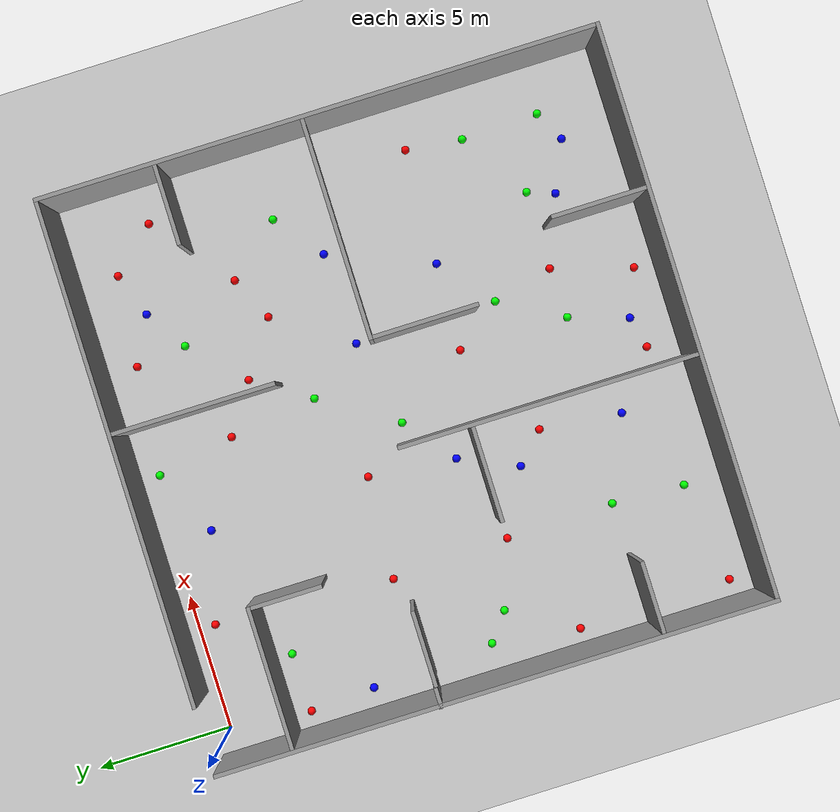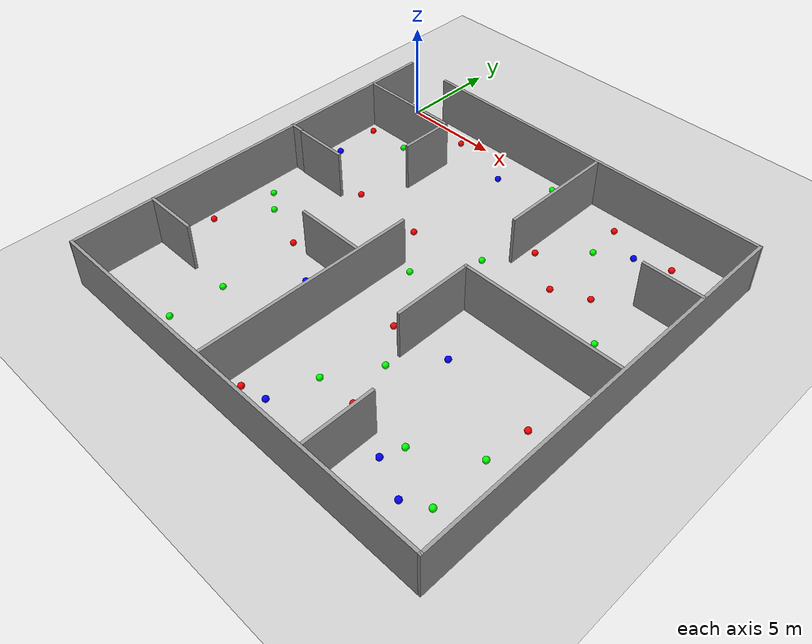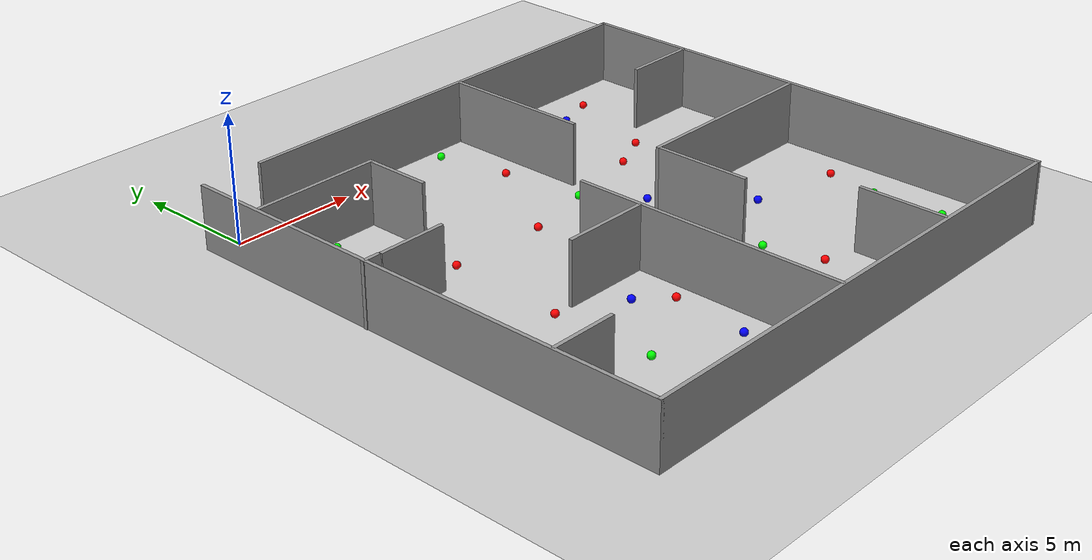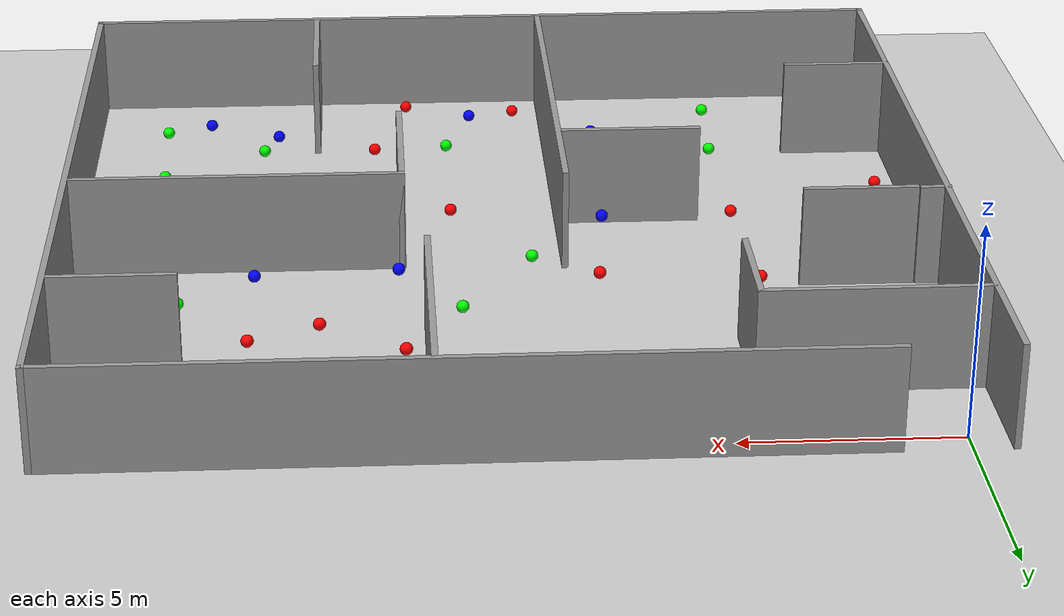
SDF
<sdf version="1.6">
 <world name="default">
  <light name="sun" type="directional">
   <pose>0 0 10 0 -0 0</pose>
   <diffuse>0.8 0.8 0.8 1</diffuse>
   <specular>0.1 0.1 0.1 1</specular>
   <attenuation>
    <range>1000</range>
    <constant>0.9</constant>
    <linear>0.01</linear>
    <quadratic>0.001</quadratic>
   </attenuation>
   <direction>-0.5 0.5 -1</direction>
  </light>
  <model name="ground_plane">
   <static>1</static>
   <link name="link">
    <collision name="collision">
     <geometry><plane><normal>0 0 1</normal><size>100 100</size></plane></geometry>
     <surface><friction><ode><mu>100</mu><mu2>50</mu2></ode></friction></surface>
    </collision>
    <visual name="visual">
     <cast_shadows>0</cast_shadows>
     <geometry><plane><normal>0 0 1</normal><size>100 100</size></plane></geometry>
     <material>
      <script><uri>file://media/materials/scripts/gazebo.material</uri><name>Gazebo/Grey</name></script>
     </material>
    </visual>
   </link>
  </model>
  <gravity>0 0 -9.8</gravity>
  <magnetic_field>6e-06 2.3e-05 -4.2e-05</magnetic_field>
  <atmosphere type="adiabatic"/>
  <physics name="default_physics" default="0" type="ode">
   <max_step_size>0.001</max_step_size>
   <real_time_factor>1</real_time_factor>
   <real_time_update_rate>1000</real_time_update_rate>
  </physics>
  <scene><ambient>0.4 0.4 0.4 1</ambient><background>0.7 0.7 0.7 1</background><shadows>1</shadows></scene>
  <spherical_coordinates>
   <surface_model>EARTH_WGS84</surface_model>
   <latitude_deg>0</latitude_deg>
   <longitude_deg>0</longitude_deg>
   <elevation>0</elevation>
   <heading_deg>0</heading_deg>
  </spherical_coordinates>
  <model name="empty_room">
   <pose>9.495 -9.705 0 0 -0 0</pose>
   <link name="Wall_4">
    <collision name="Wall_4_Collision">
     <geometry><box><size>20.5 0.15 2.5</size></box></geometry>
     <pose>0 0 1.25 0 -0 0</pose>
    </collision>
    <visual name="Wall_4_Visual">
     <pose>0 0 1.25 0 -0 0</pose>
     <geometry><box><size>20.5 0.15 2.5</size></box></geometry>
     <material>
      <script><uri>file://media/materials/scripts/gazebo.material</uri><name>Gazebo/Grey</name></script>
      <ambient>1 1 1 1</ambient>
     </material>
    </visual>
    <pose>-10.425 0 0 0 0 -1.5708</pose>
   </link>
   <link name="Wall_5">
    <collision name="Wall_5_Collision">
     <geometry><box><size>21 0.15 2.5</size></box></geometry>
     <pose>0 0 1.25 0 -0 0</pose>
    </collision>
    <visual name="Wall_5_Visual">
     <pose>0 0 1.25 0 -0 0</pose>
     <geometry><box><size>21 0.15 2.5</size></box></geometry>
     <material>
      <script><uri>file://media/materials/scripts/gazebo.material</uri><name>Gazebo/Grey</name></script>
      <ambient>1 1 1 1</ambient>
     </material>
    </visual>
    <pose>0 -10.175 0 0 -0 0</pose>
   </link>
   <link name="Wall_6">
    <collision name="Wall_6_Collision">
     <geometry><box><size>20.5 0.15 2.5</size></box></geometry>
     <pose>0 0 1.25 0 -0 0</pose>
    </collision>
    <visual name="Wall_6_Visual">
     <pose>0 0 1.25 0 -0 0</pose>
     <geometry><box><size>20.5 0.15 2.5</size></box></geometry>
     <material>
      <script><uri>file://media/materials/scripts/gazebo.material</uri><name>Gazebo/Grey</name></script>
      <ambient>1 1 1 1</ambient>
     </material>
    </visual>
    <pose>10.425 0 0 0 -0 1.5708</pose>
   </link>
   <link name="Wall_7">
    <collision name="Wall_7_Collision">
     <geometry><box><size>18.5 0.15 2.5</size></box></geometry>
     <pose>0 0 1.25 0 -0 0</pose>
    </collision>
    <visual name="Wall_7_Visual">
     <pose>0 0 1.25 0 -0 0</pose>
     <geometry><box><size>18.5 0.15 2.5</size></box></geometry>
     <material>
      <script><uri>file://media/materials/scripts/gazebo.material</uri><name>Gazebo/Grey</name></script>
      <ambient>1 1 1 1</ambient>
     </material>
    </visual>
    <pose>1.25 10.175 0 0 -0 3.14159</pose>
   </link>
   <static>1</static>
  </model>
  <model name="little_room">
   <pose>9.47484 -9.72783 0 0 -0 0</pose>
   <link name="Wall_15">
    <collision name="Wall_15_Collision">
     <geometry><box><size>11 0.15 2.5</size></box></geometry>
     <pose>0 0 1.25 0 -0 0</pose>
    </collision>
    <visual name="Wall_15_Visual">
     <pose>0 0 1.25 0 -0 0</pose>
     <geometry><box><size>11 0.15 2.5</size></box></geometry>
     <material>
      <script><uri>file://media/materials/scripts/gazebo.material</uri><name>Gazebo/Grey</name></script>
      <ambient>1 1 1 1</ambient>
     </material>
    </visual>
    <pose>-1.47005 -4.68117 0 0 -0 1.5708</pose>
   </link>
   <link name="Wall_17">
    <collision name="Wall_17_Collision">
     <geometry><box><size>8 0.15 2.5</size></box></geometry>
     <pose>0 0 1.25 0 -0 0</pose>
    </collision>
    <visual name="Wall_17_Visual">
     <pose>0 0 1.25 0 -0 0</pose>
     <geometry><box><size>8 0.15 2.5</size></box></geometry>
     <material>
      <script><uri>file://media/materials/scripts/gazebo.material</uri><name>Gazebo/Grey</name></script>
      <ambient>1 1 1 1</ambient>
     </material>
    </visual>
    <pose>6.36864 0.578681 0 0 -0 0</pose>
   </link>
   <link name="Wall_2">
    <collision name="Wall_2_Collision">
     <geometry><box><size>5.25 0.15 2.5</size></box></geometry>
     <pose>0 0 1.25 0 -0 0</pose>
    </collision>
    <visual name="Wall_2_Visual">
     <pose>0 0 1.25 0 -0 0</pose>
     <geometry><box><size>5.25 0.15 2.5</size></box></geometry>
     <material>
      <script><uri>file://media/materials/scripts/gazebo.material</uri><name>Gazebo/Grey</name></script>
      <ambient>1 1 1 1</ambient>
     </material>
    </visual>
    <pose>-7.78484 7.39778 0 0 -0 0</pose>
   </link>
   <link name="Wall_21">
    <collision name="Wall_21_Collision">
     <geometry><box><size>6 0.15 2.5</size></box></geometry>
     <pose>0 0 1.25 0 -0 0</pose>
    </collision>
    <visual name="Wall_21_Visual">
     <pose>0 0 1.25 0 -0 0</pose>
     <geometry><box><size>6 0.15 2.5</size></box></geometry>
     <material>
      <script><uri>file://media/materials/scripts/gazebo.material</uri><name>Gazebo/Grey</name></script>
      <ambient>1 1 1 1</ambient>
     </material>
    </visual>
    <pose>1.9334 7.18117 0 0 0 -1.5708</pose>
   </link>
   <link name="Wall_23">
    <collision name="Wall_23_Collision">
     <geometry><box><size>2.75 0.15 2.5</size></box></geometry>
     <pose>0 0 1.25 0 -0 0</pose>
    </collision>
    <visual name="Wall_23_Visual">
     <pose>0 0 1.25 0 -0 0</pose>
     <geometry><box><size>2.75 0.15 2.5</size></box></geometry>
     <material>
      <script><uri>file://media/materials/scripts/gazebo.material</uri><name>Gazebo/Grey</name></script>
      <ambient>1 1 1 1</ambient>
     </material>
    </visual>
    <pose>-8.3666 2.00617 0 0 -0 0</pose>
   </link>
   <link name="Wall_25">
    <collision name="Wall_25_Collision">
     <geometry><box><size>4 0.15 2.5</size></box></geometry>
     <pose>0 0 1.25 0 -0 0</pose>
    </collision>
    <visual name="Wall_25_Visual">
     <pose>0 0 1.25 0 -0 0</pose>
     <geometry><box><size>4 0.15 2.5</size></box></geometry>
     <material>
      <script><uri>file://media/materials/scripts/gazebo.material</uri><name>Gazebo/Grey</name></script>
      <ambient>1 1 1 1</ambient>
     </material>
    </visual>
    <pose>2.44364 -1.34632 0 0 0 -1.5708</pose>
   </link>
   <link name="Wall_28">
    <collision name="Wall_28_Collision">
     <geometry><box><size>3.5 0.15 2.5</size></box></geometry>
     <pose>0 0 1.25 0 -0 0</pose>
    </collision>
    <visual name="Wall_28_Visual">
     <pose>0 0 1.25 0 -0 0</pose>
     <geometry><box><size>3.5 0.15 2.5</size></box></geometry>
     <material>
      <script><uri>file://media/materials/scripts/gazebo.material</uri><name>Gazebo/Grey</name></script>
      <ambient>1 1 1 1</ambient>
     </material>
    </visual>
    <pose>-3.25737 -1.88188 0 0 -0 3.14159</pose>
   </link>
   <link name="Wall_3">
    <collision name="Wall_3_Collision">
     <geometry><box><size>2.75 0.15 2.5</size></box></geometry>
     <pose>0 0 1.25 0 -0 0</pose>
    </collision>
    <visual name="Wall_3_Visual">
     <pose>0 0 1.25 0 -0 0</pose>
     <geometry><box><size>2.75 0.15 2.5</size></box></geometry>
     <material>
      <script><uri>file://media/materials/scripts/gazebo.material</uri><name>Gazebo/Grey</name></script>
      <ambient>1 1 1 1</ambient>
     </material>
    </visual>
    <pose>-5.23484 6.09778 0 0 0 -1.5708</pose>
   </link>
   <link name="Wall_30">
    <collision name="Wall_30_Collision">
     <geometry><box><size>3.5 0.15 2.5</size></box></geometry>
     <pose>0 0 1.25 0 -0 0</pose>
    </collision>
    <visual name="Wall_30_Visual">
     <pose>0 0 1.25 0 -0 0</pose>
     <geometry><box><size>3.5 0.15 2.5</size></box></geometry>
     <material>
      <script><uri>file://media/materials/scripts/gazebo.material</uri><name>Gazebo/Grey</name></script>
      <ambient>1 1 1 1</ambient>
     </material>
    </visual>
    <pose>4.56112 -8.37241 0 0 -0 1.5708</pose>
   </link>
   <link name="Wall_33">
    <collision name="Wall_33_Collision">
     <geometry><box><size>3 0.15 2.5</size></box></geometry>
     <pose>0 0 1.25 0 -0 0</pose>
    </collision>
    <visual name="Wall_33_Visual">
     <pose>0 0 1.25 0 -0 0</pose>
     <geometry><box><size>3 0.15 2.5</size></box></geometry>
     <material>
      <script><uri>file://media/materials/scripts/gazebo.material</uri><name>Gazebo/Grey</name></script>
      <ambient>1 1 1 1</ambient>
     </material>
    </visual>
    <pose>8.97231 5.91507 0 0 -0 3.14159</pose>
   </link>
   <link name="Wall_7">
    <collision name="Wall_7_Collision">
     <geometry><box><size>2.75 0.15 2.5</size></box></geometry>
     <pose>0 0 1.25 0 -0 0</pose>
    </collision>
    <visual name="Wall_7_Visual">
     <pose>0 0 1.25 0 -0 0</pose>
     <geometry><box><size>2.75 0.15 2.5</size></box></geometry>
     <material>
      <script><uri>file://media/materials/scripts/gazebo.material</uri><name>Gazebo/Grey</name></script>
      <ambient>1 1 1 1</ambient>
     </material>
    </visual>
    <pose>-9.09731 -6.06473 0 0 -0 3.14159</pose>
   </link>
   <static>1</static>
  </model>
  <model name="merdobot_build_son">
   <pose>-0.657627 -7.68618 0 0 -0 0</pose>
   <link name="Wall_10">
    <collision name="Wall_10_Collision">
     <geometry><box><size>0.75 0.15 2.5</size></box></geometry>
     <pose>0 0 1.25 0 -0 0</pose>
    </collision>
    <visual name="Wall_10_Visual">
     <pose>0 0 1.25 0 -0 0</pose>
     <geometry><box><size>0.75 0.15 2.5</size></box></geometry>
     <material>
      <script><uri>file://media/materials/scripts/gazebo.material</uri><name>Gazebo/Grey</name></script>
      <ambient>1 1 1 1</ambient>
     </material>
    </visual>
    <pose>0 0 0 0 -0 3.14159</pose>
   </link>
   <static>1</static>
  </model>
  <model name="merdobot_world_model_son_1">
   <link name="link_2">
    <pose>-2.12823 -0.680649 -0.423559 0 -0 0</pose>
    <inertial>
     <mass>0.001</mass>
     <inertia><ixx>0.1</ixx><ixy>0</ixy><ixz>0</ixz><iyy>0.1</iyy><iyz>0</iyz><izz>0.1</izz></inertia>
    </inertial>
    <visual name="visual">
     <geometry><sphere><radius>0.15</radius></sphere></geometry>
     <material>
      <lighting>1</lighting>
      <script><uri>file://media/materials/scripts/gazebo.material</uri><name>Gazebo/Grey</name></script>
      <ambient>1 0 0 0</ambient>
      <diffuse>1 0 0 0</diffuse>
      <specular>1 0 0 0</specular>
      <emissive>0 0 0 1</emissive>
      <shader type="vertex"><normal_map>__default__</normal_map></shader>
     </material>
    </visual>
    <collision name="collision">
     <geometry><sphere><radius>0.15</radius></sphere></geometry>
     <surface>
      <friction>
       <ode><mu>1</mu><mu2>1</mu2><fdir1>0 0 0</fdir1><slip1>0</slip1><slip2>0</slip2></ode>
       <torsional>
        <coefficient>1</coefficient>
        <patch_radius>0</patch_radius>
        <surface_radius>0</surface_radius>
        <use_patch_radius>1</use_patch_radius>
        <ode><slip>0</slip></ode>
       </torsional>
      </friction>
      <bounce><restitution_coefficient>0</restitution_coefficient><threshold>1e+06</threshold></bounce>
      <contact>
       <collide_without_contact>0</collide_without_contact>
       <collide_without_contact_bitmask>1</collide_without_contact_bitmask>
       <collide_bitmask>1</collide_bitmask>
       <ode>
        <soft_cfm>0</soft_cfm>
        <soft_erp>0.2</soft_erp>
        <kp>1e+13</kp>
        <kd>1</kd>
        <max_vel>0.01</max_vel>
        <min_depth>0</min_depth>
       </ode>
       <bullet>
        <split_impulse>1</split_impulse>
        <split_impulse_penetration_threshold>-0.01</split_impulse_penetration_threshold>
        <soft_cfm>0</soft_cfm>
        <soft_erp>0.2</soft_erp>
        <kp>1e+13</kp>
        <kd>1</kd>
       </bullet>
      </contact>
     </surface>
    </collision>
   </link>
   <link name="link_2_clone">
    <pose>1.92987 1.72999 -0.413772 0 -0 0</pose>
    <inertial>
     <mass>0.001</mass>
     <inertia><ixx>0.1</ixx><ixy>0</ixy><ixz>0</ixz><iyy>0.1</iyy><iyz>0</iyz><izz>0.1</izz></inertia>
    </inertial>
    <visual name="visual">
     <geometry><sphere><radius>0.15</radius></sphere></geometry>
     <material>
      <lighting>1</lighting>
      <script><uri>file://media/materials/scripts/gazebo.material</uri><name>Gazebo/Grey</name></script>
      <ambient>1 0 0 0</ambient>
      <diffuse>1 0 0 0</diffuse>
      <specular>1 0 0 0</specular>
      <emissive>1 0 0 0</emissive>
      <shader type="vertex"><normal_map>__default__</normal_map></shader>
     </material>
    </visual>
    <collision name="collision">
     <geometry><sphere><radius>0.15</radius></sphere></geometry>
     <surface>
      <friction>
       <ode><mu>1</mu><mu2>1</mu2><fdir1>0 0 0</fdir1><slip1>0</slip1><slip2>0</slip2></ode>
       <torsional>
        <coefficient>1</coefficient>
        <patch_radius>0</patch_radius>
        <surface_radius>0</surface_radius>
        <use_patch_radius>1</use_patch_radius>
        <ode><slip>0</slip></ode>
       </torsional>
      </friction>
      <bounce><restitution_coefficient>0</restitution_coefficient><threshold>1e+06</threshold></bounce>
      <contact>
       <collide_without_contact>0</collide_without_contact>
       <collide_without_contact_bitmask>1</collide_without_contact_bitmask>
       <collide_bitmask>1</collide_bitmask>
       <ode>
        <soft_cfm>0</soft_cfm>
        <soft_erp>0.2</soft_erp>
        <kp>1e+13</kp>
        <kd>1</kd>
        <max_vel>0.01</max_vel>
        <min_depth>0</min_depth>
       </ode>
       <bullet>
        <split_impulse>1</split_impulse>
        <split_impulse_penetration_threshold>-0.01</split_impulse_penetration_threshold>
        <soft_cfm>0</soft_cfm>
        <soft_erp>0.2</soft_erp>
        <kp>1e+13</kp>
        <kd>1</kd>
       </bullet>
      </contact>
     </surface>
    </collision>
   </link>
   <link name="link_2_clone_0">
    <pose>1.61074 -4.98026 -0.15481 0 -0 0</pose>
    <inertial>
     <mass>0.001</mass>
     <inertia><ixx>0.1</ixx><ixy>0</ixy><ixz>0</ixz><iyy>0.1</iyy><iyz>0</iyz><izz>0.1</izz></inertia>
    </inertial>
    <visual name="visual">
     <geometry><sphere><radius>0.15</radius></sphere></geometry>
     <material>
      <lighting>1</lighting>
      <script><uri>file://media/materials/scripts/gazebo.material</uri><name>Gazebo/Grey</name></script>
      <ambient>1 0 0 0</ambient>
      <diffuse>1 0 0 0</diffuse>
      <specular>1 0 0 0</specular>
      <emissive>0 0 0 1</emissive>
      <shader type="vertex"><normal_map>__default__</normal_map></shader>
     </material>
    </visual>
    <collision name="collision">
     <geometry><sphere><radius>0.15</radius></sphere></geometry>
     <surface>
      <friction>
       <ode><mu>1</mu><mu2>1</mu2><fdir1>0 0 0</fdir1><slip1>0</slip1><slip2>0</slip2></ode>
       <torsional>
        <coefficient>1</coefficient>
        <patch_radius>0</patch_radius>
        <surface_radius>0</surface_radius>
        <use_patch_radius>1</use_patch_radius>
        <ode><slip>0</slip></ode>
       </torsional>
      </friction>
      <bounce><restitution_coefficient>0</restitution_coefficient><threshold>1e+06</threshold></bounce>
      <contact>
       <collide_without_contact>0</collide_without_contact>
       <collide_without_contact_bitmask>1</collide_without_contact_bitmask>
       <collide_bitmask>1</collide_bitmask>
       <ode>
        <soft_cfm>0</soft_cfm>
        <soft_erp>0.2</soft_erp>
        <kp>1e+13</kp>
        <kd>1</kd>
        <max_vel>0.01</max_vel>
        <min_depth>0</min_depth>
       </ode>
       <bullet>
        <split_impulse>1</split_impulse>
        <split_impulse_penetration_threshold>-0.01</split_impulse_penetration_threshold>
        <soft_cfm>0</soft_cfm>
        <soft_erp>0.2</soft_erp>
        <kp>1e+13</kp>
        <kd>1</kd>
       </bullet>
      </contact>
     </surface>
    </collision>
   </link>
   <link name="link_2_clone_0_clone">
    <pose>1.75573 -9.37239 -0.424203 0 -0 0</pose>
    <inertial>
     <mass>0.001</mass>
     <inertia><ixx>0.1</ixx><ixy>0</ixy><ixz>0</ixz><iyy>0.1</iyy><iyz>0</iyz><izz>0.1</izz></inertia>
    </inertial>
    <visual name="visual">
     <geometry><sphere><radius>0.15</radius></sphere></geometry>
     <material>
      <lighting>1</lighting>
      <script><uri>file://media/materials/scripts/gazebo.material</uri><name>Gazebo/Grey</name></script>
      <ambient>1 0 0 0</ambient>
      <diffuse>1 0 0 0</diffuse>
      <specular>1 0 0 0</specular>
      <emissive>0 0 0 1</emissive>
      <shader type="vertex"><normal_map>__default__</normal_map></shader>
     </material>
    </visual>
    <collision name="collision">
     <geometry><sphere><radius>0.15</radius></sphere></geometry>
     <surface>
      <friction>
       <ode><mu>1</mu><mu2>1</mu2><fdir1>0 0 0</fdir1><slip1>0</slip1><slip2>0</slip2></ode>
       <torsional>
        <coefficient>1</coefficient>
        <patch_radius>0</patch_radius>
        <surface_radius>0</surface_radius>
        <use_patch_radius>1</use_patch_radius>
        <ode><slip>0</slip></ode>
       </torsional>
      </friction>
      <bounce><restitution_coefficient>0</restitution_coefficient><threshold>1e+06</threshold></bounce>
      <contact>
       <collide_without_contact>0</collide_without_contact>
       <collide_without_contact_bitmask>1</collide_without_contact_bitmask>
       <collide_bitmask>1</collide_bitmask>
       <ode>
        <soft_cfm>0</soft_cfm>
        <soft_erp>0.2</soft_erp>
        <kp>1e+13</kp>
        <kd>1</kd>
        <max_vel>0.01</max_vel>
        <min_depth>0</min_depth>
       </ode>
       <bullet>
        <split_impulse>1</split_impulse>
        <split_impulse_penetration_threshold>-0.01</split_impulse_penetration_threshold>
        <soft_cfm>0</soft_cfm>
        <soft_erp>0.2</soft_erp>
        <kp>1e+13</kp>
        <kd>1</kd>
       </bullet>
      </contact>
     </surface>
    </collision>
   </link>
   <link name="link_2_clone_0_clone_0">
    <pose>-2.17343 -10.9359 -0.394925 0 -0 0</pose>
    <inertial>
     <mass>0.001</mass>
     <inertia><ixx>0.1</ixx><ixy>0</ixy><ixz>0</ixz><iyy>0.1</iyy><iyz>0</iyz><izz>0.1</izz></inertia>
    </inertial>
    <visual name="visual">
     <geometry><sphere><radius>0.15</radius></sphere></geometry>
     <material>
      <lighting>1</lighting>
      <script><uri>file://media/materials/scripts/gazebo.material</uri><name>Gazebo/Grey</name></script>
      <ambient>1 0 0 0</ambient>
      <diffuse>1 0 0 0</diffuse>
      <specular>1 0 0 0</specular>
      <emissive>0 0 0 1</emissive>
      <shader type="vertex"><normal_map>__default__</normal_map></shader>
     </material>
    </visual>
    <collision name="collision">
     <geometry><sphere><radius>0.15</radius></sphere></geometry>
     <surface>
      <friction>
       <ode><mu>1</mu><mu2>1</mu2><fdir1>0 0 0</fdir1><slip1>0</slip1><slip2>0</slip2></ode>
       <torsional>
        <coefficient>1</coefficient>
        <patch_radius>0</patch_radius>
        <surface_radius>0</surface_radius>
        <use_patch_radius>1</use_patch_radius>
        <ode><slip>0</slip></ode>
       </torsional>
      </friction>
      <bounce><restitution_coefficient>0</restitution_coefficient><threshold>1e+06</threshold></bounce>
      <contact>
       <collide_without_contact>0</collide_without_contact>
       <collide_without_contact_bitmask>1</collide_without_contact_bitmask>
       <collide_bitmask>1</collide_bitmask>
       <ode>
        <soft_cfm>0</soft_cfm>
        <soft_erp>0.2</soft_erp>
        <kp>1e+13</kp>
        <kd>1</kd>
        <max_vel>0.01</max_vel>
        <min_depth>0</min_depth>
       </ode>
       <bullet>
        <split_impulse>1</split_impulse>
        <split_impulse_penetration_threshold>-0.01</split_impulse_penetration_threshold>
        <soft_cfm>0</soft_cfm>
        <soft_erp>0.2</soft_erp>
        <kp>1e+13</kp>
        <kd>1</kd>
       </bullet>
      </contact>
     </surface>
    </collision>
   </link>
   <link name="link_2_clone_0_clone_0_clone">
    <pose>8.81039 -9.78149 -0.412733 0 -0 0</pose>
    <inertial>
     <mass>0.001</mass>
     <inertia><ixx>0.1</ixx><ixy>0</ixy><ixz>0</ixz><iyy>0.1</iyy><iyz>0</iyz><izz>0.1</izz></inertia>
    </inertial>
    <visual name="visual">
     <geometry><sphere><radius>0.15</radius></sphere></geometry>
     <material>
      <lighting>1</lighting>
      <script><uri>file://media/materials/scripts/gazebo.material</uri><name>Gazebo/Grey</name></script>
      <ambient>1 0 0 0</ambient>
      <diffuse>1 0 0 0</diffuse>
      <specular>1 0 0 0</specular>
      <emissive>0 0 0 1</emissive>
      <shader type="vertex"><normal_map>__default__</normal_map></shader>
     </material>
    </visual>
    <collision name="collision">
     <geometry><sphere><radius>0.15</radius></sphere></geometry>
     <surface>
      <friction>
       <ode><mu>1</mu><mu2>1</mu2><fdir1>0 0 0</fdir1><slip1>0</slip1><slip2>0</slip2></ode>
       <torsional>
        <coefficient>1</coefficient>
        <patch_radius>0</patch_radius>
        <surface_radius>0</surface_radius>
        <use_patch_radius>1</use_patch_radius>
        <ode><slip>0</slip></ode>
       </torsional>
      </friction>
      <bounce><restitution_coefficient>0</restitution_coefficient><threshold>1e+06</threshold></bounce>
      <contact>
       <collide_without_contact>0</collide_without_contact>
       <collide_without_contact_bitmask>1</collide_without_contact_bitmask>
       <collide_bitmask>1</collide_bitmask>
       <ode>
        <soft_cfm>0</soft_cfm>
        <soft_erp>0.2</soft_erp>
        <kp>1e+13</kp>
        <kd>1</kd>
        <max_vel>0.01</max_vel>
        <min_depth>0</min_depth>
       </ode>
       <bullet>
        <split_impulse>1</split_impulse>
        <split_impulse_penetration_threshold>-0.01</split_impulse_penetration_threshold>
        <soft_cfm>0</soft_cfm>
        <soft_erp>0.2</soft_erp>
        <kp>1e+13</kp>
        <kd>1</kd>
       </bullet>
      </contact>
     </surface>
    </collision>
   </link>
   <link name="link_2_clone_0_clone_0_clone_0">
    <pose>11.7404 1.62895 -0.355193 0 -0 0</pose>
    <inertial>
     <mass>0.001</mass>
     <inertia><ixx>0.1</ixx><ixy>0</ixy><ixz>0</ixz><iyy>0.1</iyy><iyz>0</iyz><izz>0.1</izz></inertia>
    </inertial>
    <visual name="visual">
     <geometry><sphere><radius>0.15</radius></sphere></geometry>
     <material>
      <lighting>1</lighting>
      <script><uri>file://media/materials/scripts/gazebo.material</uri><name>Gazebo/Grey</name></script>
      <ambient>1 0 0 0</ambient>
      <diffuse>1 0 0 0</diffuse>
      <specular>1 0 0 0</specular>
      <emissive>0 0 0 1</emissive>
      <shader type="vertex"><normal_map>__default__</normal_map></shader>
     </material>
    </visual>
    <collision name="collision">
     <geometry><sphere><radius>0.15</radius></sphere></geometry>
     <surface>
      <friction>
       <ode><mu>1</mu><mu2>1</mu2><fdir1>0 0 0</fdir1><slip1>0</slip1><slip2>0</slip2></ode>
       <torsional>
        <coefficient>1</coefficient>
        <patch_radius>0</patch_radius>
        <surface_radius>0</surface_radius>
        <use_patch_radius>1</use_patch_radius>
        <ode><slip>0</slip></ode>
       </torsional>
      </friction>
      <bounce><restitution_coefficient>0</restitution_coefficient><threshold>1e+06</threshold></bounce>
      <contact>
       <collide_without_contact>0</collide_without_contact>
       <collide_without_contact_bitmask>1</collide_without_contact_bitmask>
       <collide_bitmask>1</collide_bitmask>
       <ode>
        <soft_cfm>0</soft_cfm>
        <soft_erp>0.2</soft_erp>
        <kp>1e+13</kp>
        <kd>1</kd>
        <max_vel>0.01</max_vel>
        <min_depth>0</min_depth>
       </ode>
       <bullet>
        <split_impulse>1</split_impulse>
        <split_impulse_penetration_threshold>-0.01</split_impulse_penetration_threshold>
        <soft_cfm>0</soft_cfm>
        <soft_erp>0.2</soft_erp>
        <kp>1e+13</kp>
        <kd>1</kd>
       </bullet>
      </contact>
     </surface>
    </collision>
   </link>
   <link name="link_2_clone_0_clone_0_clone_0_clone">
    <pose>15.1126 1.3237 -0.420937 0 -0 0</pose>
    <inertial>
     <mass>0.001</mass>
     <inertia><ixx>0.1</ixx><ixy>0</ixy><ixz>0</ixz><iyy>0.1</iyy><iyz>0</iyz><izz>0.1</izz></inertia>
    </inertial>
    <visual name="visual">
     <geometry><sphere><radius>0.15</radius></sphere></geometry>
     <material>
      <lighting>1</lighting>
      <script><uri>file://media/materials/scripts/gazebo.material</uri><name>Gazebo/Grey</name></script>
      <ambient>1 0 0 0</ambient>
      <diffuse>1 0 0 0</diffuse>
      <specular>1 0 0 0</specular>
      <emissive>0 0 0 1</emissive>
      <shader type="vertex"><normal_map>__default__</normal_map></shader>
     </material>
    </visual>
    <collision name="collision">
     <geometry><sphere><radius>0.15</radius></sphere></geometry>
     <surface>
      <friction>
       <ode><mu>1</mu><mu2>1</mu2><fdir1>0 0 0</fdir1><slip1>0</slip1><slip2>0</slip2></ode>
       <torsional>
        <coefficient>1</coefficient>
        <patch_radius>0</patch_radius>
        <surface_radius>0</surface_radius>
        <use_patch_radius>1</use_patch_radius>
        <ode><slip>0</slip></ode>
       </torsional>
      </friction>
      <bounce><restitution_coefficient>0</restitution_coefficient><threshold>1e+06</threshold></bounce>
      <contact>
       <collide_without_contact>0</collide_without_contact>
       <collide_without_contact_bitmask>1</collide_without_contact_bitmask>
       <collide_bitmask>1</collide_bitmask>
       <ode>
        <soft_cfm>0</soft_cfm>
        <soft_erp>0.2</soft_erp>
        <kp>1e+13</kp>
        <kd>1</kd>
        <max_vel>0.01</max_vel>
        <min_depth>0</min_depth>
       </ode>
       <bullet>
        <split_impulse>1</split_impulse>
        <split_impulse_penetration_threshold>-0.01</split_impulse_penetration_threshold>
        <soft_cfm>0</soft_cfm>
        <soft_erp>0.2</soft_erp>
        <kp>1e+13</kp>
        <kd>1</kd>
       </bullet>
      </contact>
     </surface>
    </collision>
   </link>
   <link name="link_2_clone_0_clone_0_clone_clone">
    <pose>12.0514 -3.45905 -0.396188 0 -0 0</pose>
    <inertial>
     <mass>0.001</mass>
     <inertia><ixx>0.1</ixx><ixy>0</ixy><ixz>0</ixz><iyy>0.1</iyy><iyz>0</iyz><izz>0.1</izz></inertia>
    </inertial>
    <visual name="visual">
     <geometry><sphere><radius>0.15</radius></sphere></geometry>
     <material>
      <lighting>1</lighting>
      <script><uri>file://media/materials/scripts/gazebo.material</uri><name>Gazebo/Grey</name></script>
      <ambient>1 0 0 0</ambient>
      <diffuse>1 0 0 0</diffuse>
      <specular>1 0 0 0</specular>
      <emissive>0 0 0 1</emissive>
      <shader type="vertex"><normal_map>__default__</normal_map></shader>
     </material>
    </visual>
    <collision name="collision">
     <geometry><sphere><radius>0.15</radius></sphere></geometry>
     <surface>
      <friction>
       <ode><mu>1</mu><mu2>1</mu2><fdir1>0 0 0</fdir1><slip1>0</slip1><slip2>0</slip2></ode>
       <torsional>
        <coefficient>1</coefficient>
        <patch_radius>0</patch_radius>
        <surface_radius>0</surface_radius>
        <use_patch_radius>1</use_patch_radius>
        <ode><slip>0</slip></ode>
       </torsional>
      </friction>
      <bounce><restitution_coefficient>0</restitution_coefficient><threshold>1e+06</threshold></bounce>
      <contact>
       <collide_without_contact>0</collide_without_contact>
       <collide_without_contact_bitmask>1</collide_without_contact_bitmask>
       <collide_bitmask>1</collide_bitmask>
       <ode>
        <soft_cfm>0</soft_cfm>
        <soft_erp>0.2</soft_erp>
        <kp>1e+13</kp>
        <kd>1</kd>
        <max_vel>0.01</max_vel>
        <min_depth>0</min_depth>
       </ode>
       <bullet>
        <split_impulse>1</split_impulse>
        <split_impulse_penetration_threshold>-0.01</split_impulse_penetration_threshold>
        <soft_cfm>0</soft_cfm>
        <soft_erp>0.2</soft_erp>
        <kp>1e+13</kp>
        <kd>1</kd>
       </bullet>
      </contact>
     </surface>
    </collision>
   </link>
   <link name="link_2_clone_0_clone_0_clone_clone_0_clone">
    <pose>9.79759 -16.7248 -0.393938 0 -0 0</pose>
    <inertial>
     <mass>0.001</mass>
     <inertia><ixx>0.1</ixx><ixy>0</ixy><ixz>0</ixz><iyy>0.1</iyy><iyz>0</iyz><izz>0.1</izz></inertia>
    </inertial>
    <visual name="visual">
     <geometry><sphere><radius>0.15</radius></sphere></geometry>
     <material>
      <lighting>1</lighting>
      <script><uri>file://media/materials/scripts/gazebo.material</uri><name>Gazebo/Grey</name></script>
      <ambient>1 0 0 0</ambient>
      <diffuse>1 0 0 0</diffuse>
      <specular>1 0 0 0</specular>
      <emissive>0 0 0 1</emissive>
      <shader type="vertex"><normal_map>__default__</normal_map></shader>
     </material>
    </visual>
    <collision name="collision">
     <geometry><sphere><radius>0.15</radius></sphere></geometry>
     <surface>
      <friction>
       <ode><mu>1</mu><mu2>1</mu2><fdir1>0 0 0</fdir1><slip1>0</slip1><slip2>0</slip2></ode>
       <torsional>
        <coefficient>1</coefficient>
        <patch_radius>0</patch_radius>
        <surface_radius>0</surface_radius>
        <use_patch_radius>1</use_patch_radius>
        <ode><slip>0</slip></ode>
       </torsional>
      </friction>
      <bounce><restitution_coefficient>0</restitution_coefficient><threshold>1e+06</threshold></bounce>
      <contact>
       <collide_without_contact>0</collide_without_contact>
       <collide_without_contact_bitmask>1</collide_without_contact_bitmask>
       <collide_bitmask>1</collide_bitmask>
       <ode>
        <soft_cfm>0</soft_cfm>
        <soft_erp>0.2</soft_erp>
        <kp>1e+13</kp>
        <kd>1</kd>
        <max_vel>0.01</max_vel>
        <min_depth>0</min_depth>
       </ode>
       <bullet>
        <split_impulse>1</split_impulse>
        <split_impulse_penetration_threshold>-0.01</split_impulse_penetration_threshold>
        <soft_cfm>0</soft_cfm>
        <soft_erp>0.2</soft_erp>
        <kp>1e+13</kp>
        <kd>1</kd>
       </bullet>
      </contact>
     </surface>
    </collision>
   </link>
   <link name="link_2_clone_0_clone_0_clone_clone_0_clone_clone">
    <pose>6.89703 -16.3138 -0.405701 0 -0 0</pose>
    <inertial>
     <mass>0.001</mass>
     <inertia><ixx>0.1</ixx><ixy>0</ixy><ixz>0</ixz><iyy>0.1</iyy><iyz>0</iyz><izz>0.1</izz></inertia>
    </inertial>
    <visual name="visual">
     <geometry><sphere><radius>0.15</radius></sphere></geometry>
     <material>
      <lighting>1</lighting>
      <script><uri>file://media/materials/scripts/gazebo.material</uri><name>Gazebo/Grey</name></script>
      <ambient>1 0 0 0</ambient>
      <diffuse>1 0 0 0</diffuse>
      <specular>1 0 0 0</specular>
      <emissive>0 0 0 1</emissive>
      <shader type="vertex"><normal_map>__default__</normal_map></shader>
     </material>
    </visual>
    <collision name="collision">
     <geometry><sphere><radius>0.15</radius></sphere></geometry>
     <surface>
      <friction>
       <ode><mu>1</mu><mu2>1</mu2><fdir1>0 0 0</fdir1><slip1>0</slip1><slip2>0</slip2></ode>
       <torsional>
        <coefficient>1</coefficient>
        <patch_radius>0</patch_radius>
        <surface_radius>0</surface_radius>
        <use_patch_radius>1</use_patch_radius>
        <ode><slip>0</slip></ode>
       </torsional>
      </friction>
      <bounce><restitution_coefficient>0</restitution_coefficient><threshold>1e+06</threshold></bounce>
      <contact>
       <collide_without_contact>0</collide_without_contact>
       <collide_without_contact_bitmask>1</collide_without_contact_bitmask>
       <collide_bitmask>1</collide_bitmask>
       <ode>
        <soft_cfm>0</soft_cfm>
        <soft_erp>0.2</soft_erp>
        <kp>1e+13</kp>
        <kd>1</kd>
        <max_vel>0.01</max_vel>
        <min_depth>0</min_depth>
       </ode>
       <bullet>
        <split_impulse>1</split_impulse>
        <split_impulse_penetration_threshold>-0.01</split_impulse_penetration_threshold>
        <soft_cfm>0</soft_cfm>
        <soft_erp>0.2</soft_erp>
        <kp>1e+13</kp>
        <kd>1</kd>
       </bullet>
      </contact>
     </surface>
    </collision>
   </link>
   <link name="link_2_clone_0_clone_0_clone_clone_1">
    <pose>10.6799 -13.781 -0.403389 0 -0.029702 0</pose>
    <inertial>
     <mass>0.001</mass>
     <inertia><ixx>0.1</ixx><ixy>0</ixy><ixz>0</ixz><iyy>0.1</iyy><iyz>0</iyz><izz>0.1</izz></inertia>
    </inertial>
    <visual name="visual">
     <geometry><sphere><radius>0.15</radius></sphere></geometry>
     <material>
      <lighting>1</lighting>
      <script><uri>file://media/materials/scripts/gazebo.material</uri><name>Gazebo/Grey</name></script>
      <ambient>1 0 0 0</ambient>
      <diffuse>1 0 0 0</diffuse>
      <specular>1 0 0 0</specular>
      <emissive>0 0 0 1</emissive>
      <shader type="vertex"><normal_map>__default__</normal_map></shader>
     </material>
    </visual>
    <collision name="collision">
     <geometry><sphere><radius>0.15</radius></sphere></geometry>
     <surface>
      <friction>
       <ode><mu>1</mu><mu2>1</mu2><fdir1>0 0 0</fdir1><slip1>0</slip1><slip2>0</slip2></ode>
       <torsional>
        <coefficient>1</coefficient>
        <patch_radius>0</patch_radius>
        <surface_radius>0</surface_radius>
        <use_patch_radius>1</use_patch_radius>
        <ode><slip>0</slip></ode>
       </torsional>
      </friction>
      <bounce><restitution_coefficient>0</restitution_coefficient><threshold>1e+06</threshold></bounce>
      <contact>
       <collide_without_contact>0</collide_without_contact>
       <collide_without_contact_bitmask>1</collide_without_contact_bitmask>
       <collide_bitmask>1</collide_bitmask>
       <ode>
        <soft_cfm>0</soft_cfm>
        <soft_erp>0.2</soft_erp>
        <kp>1e+13</kp>
        <kd>1</kd>
        <max_vel>0.01</max_vel>
        <min_depth>0</min_depth>
       </ode>
       <bullet>
        <split_impulse>1</split_impulse>
        <split_impulse_penetration_threshold>-0.01</split_impulse_penetration_threshold>
        <soft_cfm>0</soft_cfm>
        <soft_erp>0.2</soft_erp>
        <kp>1e+13</kp>
        <kd>1</kd>
       </bullet>
      </contact>
     </surface>
    </collision>
   </link>
   <link name="link_2_clone_0_clone_0_clone_clone_clone">
    <pose>13.6924 -2.68946 -0.400272 0 -0 0</pose>
    <inertial>
     <mass>0.001</mass>
     <inertia><ixx>0.1</ixx><ixy>0</ixy><ixz>0</ixz><iyy>0.1</iyy><iyz>0</iyz><izz>0.1</izz></inertia>
    </inertial>
    <visual name="visual">
     <geometry><sphere><radius>0.15</radius></sphere></geometry>
     <material>
      <lighting>1</lighting>
      <script><uri>file://media/materials/scripts/gazebo.material</uri><name>Gazebo/Grey</name></script>
      <ambient>1 0 0 0</ambient>
      <diffuse>1 0 0 0</diffuse>
      <specular>1 0 0 0</specular>
      <emissive>0 0 0 1</emissive>
      <shader type="vertex"><normal_map>__default__</normal_map></shader>
     </material>
    </visual>
    <collision name="collision">
     <geometry><sphere><radius>0.15</radius></sphere></geometry>
     <surface>
      <friction>
       <ode><mu>1</mu><mu2>1</mu2><fdir1>0 0 0</fdir1><slip1>0</slip1><slip2>0</slip2></ode>
       <torsional>
        <coefficient>1</coefficient>
        <patch_radius>0</patch_radius>
        <surface_radius>0</surface_radius>
        <use_patch_radius>1</use_patch_radius>
        <ode><slip>0</slip></ode>
       </torsional>
      </friction>
      <bounce><restitution_coefficient>0</restitution_coefficient><threshold>1e+06</threshold></bounce>
      <contact>
       <collide_without_contact>0</collide_without_contact>
       <collide_without_contact_bitmask>1</collide_without_contact_bitmask>
       <collide_bitmask>1</collide_bitmask>
       <ode>
        <soft_cfm>0</soft_cfm>
        <soft_erp>0.2</soft_erp>
        <kp>1e+13</kp>
        <kd>1</kd>
        <max_vel>0.01</max_vel>
        <min_depth>0</min_depth>
       </ode>
       <bullet>
        <split_impulse>1</split_impulse>
        <split_impulse_penetration_threshold>-0.01</split_impulse_penetration_threshold>
        <soft_cfm>0</soft_cfm>
        <soft_erp>0.2</soft_erp>
        <kp>1e+13</kp>
        <kd>1</kd>
       </bullet>
      </contact>
     </surface>
    </collision>
   </link>
   <link name="link_2_clone_clone">
    <pose>5.24638 0.849767 -0.419481 0 -0.04034 0</pose>
    <inertial>
     <mass>0.001</mass>
     <inertia><ixx>0.1</ixx><ixy>0</ixy><ixz>0</ixz><iyy>0.1</iyy><iyz>0</iyz><izz>0.1</izz></inertia>
    </inertial>
    <visual name="visual">
     <geometry><sphere><radius>0.15</radius></sphere></geometry>
     <material>
      <lighting>1</lighting>
      <script><uri>file://media/materials/scripts/gazebo.material</uri><name>Gazebo/Grey</name></script>
      <ambient>0 0 1 0</ambient>
      <diffuse>0 0 1 0</diffuse>
      <specular>0 0 1 0</specular>
      <emissive>0 0 0 1</emissive>
      <shader type="vertex"><normal_map>__default__</normal_map></shader>
     </material>
    </visual>
    <collision name="collision">
     <geometry><sphere><radius>0.15</radius></sphere></geometry>
     <surface>
      <friction>
       <ode><mu>1</mu><mu2>1</mu2><fdir1>0 0 0</fdir1><slip1>0</slip1><slip2>0</slip2></ode>
       <torsional>
        <coefficient>1</coefficient>
        <patch_radius>0</patch_radius>
        <surface_radius>0</surface_radius>
        <use_patch_radius>1</use_patch_radius>
        <ode><slip>0</slip></ode>
       </torsional>
      </friction>
      <bounce><restitution_coefficient>0</restitution_coefficient><threshold>1e+06</threshold></bounce>
      <contact>
       <collide_without_contact>0</collide_without_contact>
       <collide_without_contact_bitmask>1</collide_without_contact_bitmask>
       <collide_bitmask>1</collide_bitmask>
       <ode>
        <soft_cfm>0</soft_cfm>
        <soft_erp>0.2</soft_erp>
        <kp>1e+13</kp>
        <kd>1</kd>
        <max_vel>0.01</max_vel>
        <min_depth>0</min_depth>
       </ode>
       <bullet>
        <split_impulse>1</split_impulse>
        <split_impulse_penetration_threshold>-0.01</split_impulse_penetration_threshold>
        <soft_cfm>0</soft_cfm>
        <soft_erp>0.2</soft_erp>
        <kp>1e+13</kp>
        <kd>1</kd>
       </bullet>
      </contact>
     </surface>
    </collision>
   </link>
   <link name="link_2_clone_clone_0">
    <pose>5.42014 -5.21126 -0.074857 0 -0 0</pose>
    <inertial>
     <mass>0.001</mass>
     <inertia><ixx>0.1</ixx><ixy>0</ixy><ixz>0</ixz><iyy>0.1</iyy><iyz>0</iyz><izz>0.1</izz></inertia>
    </inertial>
    <visual name="visual">
     <geometry><sphere><radius>0.15</radius></sphere></geometry>
     <material>
      <lighting>1</lighting>
      <script><uri>file://media/materials/scripts/gazebo.material</uri><name>Gazebo/Grey</name></script>
      <ambient>1 0 0 0</ambient>
      <diffuse>1 0 0 0</diffuse>
      <specular>1 0 0 0</specular>
      <emissive>1 0 0 0</emissive>
      <shader type="vertex"><normal_map>__default__</normal_map></shader>
     </material>
    </visual>
    <collision name="collision">
     <geometry><sphere><radius>0.15</radius></sphere></geometry>
     <surface>
      <friction>
       <ode><mu>1</mu><mu2>1</mu2><fdir1>0 0 0</fdir1><slip1>0</slip1><slip2>0</slip2></ode>
       <torsional>
        <coefficient>1</coefficient>
        <patch_radius>0</patch_radius>
        <surface_radius>0</surface_radius>
        <use_patch_radius>1</use_patch_radius>
        <ode><slip>0</slip></ode>
       </torsional>
      </friction>
      <bounce><restitution_coefficient>0</restitution_coefficient><threshold>1e+06</threshold></bounce>
      <contact>
       <collide_without_contact>0</collide_without_contact>
       <collide_without_contact_bitmask>1</collide_without_contact_bitmask>
       <collide_bitmask>1</collide_bitmask>
       <ode>
        <soft_cfm>0</soft_cfm>
        <soft_erp>0.2</soft_erp>
        <kp>1e+13</kp>
        <kd>1</kd>
        <max_vel>0.01</max_vel>
        <min_depth>0</min_depth>
       </ode>
       <bullet>
        <split_impulse>1</split_impulse>
        <split_impulse_penetration_threshold>-0.01</split_impulse_penetration_threshold>
        <soft_cfm>0</soft_cfm>
        <soft_erp>0.2</soft_erp>
        <kp>1e+13</kp>
        <kd>1</kd>
       </bullet>
      </contact>
     </surface>
    </collision>
   </link>
   <link name="link_2_clone_clone_0_clone_clone">
    <pose>8.27735 -0.883997 -0.372352 0 -0 0</pose>
    <inertial>
     <mass>0.001</mass>
     <inertia><ixx>0.1</ixx><ixy>0</ixy><ixz>0</ixz><iyy>0.1</iyy><iyz>0</iyz><izz>0.1</izz></inertia>
    </inertial>
    <visual name="visual">
     <geometry><sphere><radius>0.15</radius></sphere></geometry>
     <material>
      <lighting>1</lighting>
      <script><uri>file://media/materials/scripts/gazebo.material</uri><name>Gazebo/Grey</name></script>
      <ambient>1 0 0 0</ambient>
      <diffuse>1 0 0 0</diffuse>
      <specular>1 0 0 0</specular>
      <emissive>1 0 0 0</emissive>
      <shader type="vertex"><normal_map>__default__</normal_map></shader>
     </material>
    </visual>
    <collision name="collision">
     <geometry><sphere><radius>0.15</radius></sphere></geometry>
     <surface>
      <friction>
       <ode><mu>1</mu><mu2>1</mu2><fdir1>0 0 0</fdir1><slip1>0</slip1><slip2>0</slip2></ode>
       <torsional>
        <coefficient>1</coefficient>
        <patch_radius>0</patch_radius>
        <surface_radius>0</surface_radius>
        <use_patch_radius>1</use_patch_radius>
        <ode><slip>0</slip></ode>
       </torsional>
      </friction>
      <bounce><restitution_coefficient>0</restitution_coefficient><threshold>1e+06</threshold></bounce>
      <contact>
       <collide_without_contact>0</collide_without_contact>
       <collide_without_contact_bitmask>1</collide_without_contact_bitmask>
       <collide_bitmask>1</collide_bitmask>
       <ode>
        <soft_cfm>0</soft_cfm>
        <soft_erp>0.2</soft_erp>
        <kp>1e+13</kp>
        <kd>1</kd>
        <max_vel>0.01</max_vel>
        <min_depth>0</min_depth>
       </ode>
       <bullet>
        <split_impulse>1</split_impulse>
        <split_impulse_penetration_threshold>-0.01</split_impulse_penetration_threshold>
        <soft_cfm>0</soft_cfm>
        <soft_erp>0.2</soft_erp>
        <kp>1e+13</kp>
        <kd>1</kd>
       </bullet>
      </contact>
     </surface>
    </collision>
   </link>
   <link name="link_2_clone_clone_0_clone_clone_0">
    <pose>5.19309 -11.6666 -0.383794 0 -0 0</pose>
    <inertial>
     <mass>0.001</mass>
     <inertia><ixx>0.1</ixx><ixy>0</ixy><ixz>0</ixz><iyy>0.1</iyy><iyz>0</iyz><izz>0.1</izz></inertia>
    </inertial>
    <visual name="visual">
     <geometry><sphere><radius>0.15</radius></sphere></geometry>
     <material>
      <lighting>1</lighting>
      <script><uri>file://media/materials/scripts/gazebo.material</uri><name>Gazebo/Grey</name></script>
      <ambient>1 0 0 0</ambient>
      <diffuse>1 0 0 0</diffuse>
      <specular>1 0 0 0</specular>
      <emissive>1 0 0 0</emissive>
      <shader type="vertex"><normal_map>__default__</normal_map></shader>
     </material>
    </visual>
    <collision name="collision">
     <geometry><sphere><radius>0.15</radius></sphere></geometry>
     <surface>
      <friction>
       <ode><mu>1</mu><mu2>1</mu2><fdir1>0 0 0</fdir1><slip1>0</slip1><slip2>0</slip2></ode>
       <torsional>
        <coefficient>1</coefficient>
        <patch_radius>0</patch_radius>
        <surface_radius>0</surface_radius>
        <use_patch_radius>1</use_patch_radius>
        <ode><slip>0</slip></ode>
       </torsional>
      </friction>
      <bounce><restitution_coefficient>0</restitution_coefficient><threshold>1e+06</threshold></bounce>
      <contact>
       <collide_without_contact>0</collide_without_contact>
       <collide_without_contact_bitmask>1</collide_without_contact_bitmask>
       <collide_bitmask>1</collide_bitmask>
       <ode>
        <soft_cfm>0</soft_cfm>
        <soft_erp>0.2</soft_erp>
        <kp>1e+13</kp>
        <kd>1</kd>
        <max_vel>0.01</max_vel>
        <min_depth>0</min_depth>
       </ode>
       <bullet>
        <split_impulse>1</split_impulse>
        <split_impulse_penetration_threshold>-0.01</split_impulse_penetration_threshold>
        <soft_cfm>0</soft_cfm>
        <soft_erp>0.2</soft_erp>
        <kp>1e+13</kp>
        <kd>1</kd>
       </bullet>
      </contact>
     </surface>
    </collision>
   </link>
   <link name="link_2_clone_clone_0_clone_clone_0_clone">
    <pose>10.0765 -2.09639 -0.392024 0 -0 0</pose>
    <inertial>
     <mass>0.001</mass>
     <inertia><ixx>0.1</ixx><ixy>0</ixy><ixz>0</ixz><iyy>0.1</iyy><iyz>0</iyz><izz>0.1</izz></inertia>
    </inertial>
    <visual name="visual">
     <geometry><sphere><radius>0.15</radius></sphere></geometry>
     <material>
      <lighting>1</lighting>
      <script><uri>file://media/materials/scripts/gazebo.material</uri><name>Gazebo/Grey</name></script>
      <ambient>1 0 0 0</ambient>
      <diffuse>1 0 0 0</diffuse>
      <specular>1 0 0 0</specular>
      <emissive>1 0 0 0</emissive>
      <shader type="vertex"><normal_map>__default__</normal_map></shader>
     </material>
    </visual>
    <collision name="collision">
     <geometry><sphere><radius>0.15</radius></sphere></geometry>
     <surface>
      <friction>
       <ode><mu>1</mu><mu2>1</mu2><fdir1>0 0 0</fdir1><slip1>0</slip1><slip2>0</slip2></ode>
       <torsional>
        <coefficient>1</coefficient>
        <patch_radius>0</patch_radius>
        <surface_radius>0</surface_radius>
        <use_patch_radius>1</use_patch_radius>
        <ode><slip>0</slip></ode>
       </torsional>
      </friction>
      <bounce><restitution_coefficient>0</restitution_coefficient><threshold>1e+06</threshold></bounce>
      <contact>
       <collide_without_contact>0</collide_without_contact>
       <collide_without_contact_bitmask>1</collide_without_contact_bitmask>
       <collide_bitmask>1</collide_bitmask>
       <ode>
        <soft_cfm>0</soft_cfm>
        <soft_erp>0.2</soft_erp>
        <kp>1e+13</kp>
        <kd>1</kd>
        <max_vel>0.01</max_vel>
        <min_depth>0</min_depth>
       </ode>
       <bullet>
        <split_impulse>1</split_impulse>
        <split_impulse_penetration_threshold>-0.01</split_impulse_penetration_threshold>
        <soft_cfm>0</soft_cfm>
        <soft_erp>0.2</soft_erp>
        <kp>1e+13</kp>
        <kd>1</kd>
       </bullet>
      </contact>
     </surface>
    </collision>
   </link>
   <link name="link_2_clone_clone_0_clone_clone_0_clone_clone">
    <pose>16.5803 -0.322892 -0.3281 0 -0 0</pose>
    <inertial>
     <mass>0.001</mass>
     <inertia><ixx>0.1</ixx><ixy>0</ixy><ixz>0</ixz><iyy>0.1</iyy><iyz>0</iyz><izz>0.1</izz></inertia>
    </inertial>
    <visual name="visual">
     <geometry><sphere><radius>0.15</radius></sphere></geometry>
     <material>
      <lighting>1</lighting>
      <script><uri>file://media/materials/scripts/gazebo.material</uri><name>Gazebo/Grey</name></script>
      <ambient>1 0 0 0</ambient>
      <diffuse>1 0 0 0</diffuse>
      <specular>1 0 0 0</specular>
      <emissive>1 0 0 0</emissive>
      <shader type="vertex"><normal_map>__default__</normal_map></shader>
     </material>
    </visual>
    <collision name="collision">
     <geometry><sphere><radius>0.15</radius></sphere></geometry>
     <surface>
      <friction>
       <ode><mu>1</mu><mu2>1</mu2><fdir1>0 0 0</fdir1><slip1>0</slip1><slip2>0</slip2></ode>
       <torsional>
        <coefficient>1</coefficient>
        <patch_radius>0</patch_radius>
        <surface_radius>0</surface_radius>
        <use_patch_radius>1</use_patch_radius>
        <ode><slip>0</slip></ode>
       </torsional>
      </friction>
      <bounce><restitution_coefficient>0</restitution_coefficient><threshold>1e+06</threshold></bounce>
      <contact>
       <collide_without_contact>0</collide_without_contact>
       <collide_without_contact_bitmask>1</collide_without_contact_bitmask>
       <collide_bitmask>1</collide_bitmask>
       <ode>
        <soft_cfm>0</soft_cfm>
        <soft_erp>0.2</soft_erp>
        <kp>1e+13</kp>
        <kd>1</kd>
        <max_vel>0.01</max_vel>
        <min_depth>0</min_depth>
       </ode>
       <bullet>
        <split_impulse>1</split_impulse>
        <split_impulse_penetration_threshold>-0.01</split_impulse_penetration_threshold>
        <soft_cfm>0</soft_cfm>
        <soft_erp>0.2</soft_erp>
        <kp>1e+13</kp>
        <kd>1</kd>
       </bullet>
      </contact>
     </surface>
    </collision>
   </link>
   <link name="link_2_clone_clone_0_clone_clone_0_clone_clone_clone">
    <pose>16.3559 -10.0424 -0.329384 0 -0 0</pose>
    <inertial>
     <mass>0.001</mass>
     <inertia><ixx>0.1</ixx><ixy>0</ixy><ixz>0</ixz><iyy>0.1</iyy><iyz>0</iyz><izz>0.1</izz></inertia>
    </inertial>
    <visual name="visual">
     <geometry><sphere><radius>0.15</radius></sphere></geometry>
     <material>
      <lighting>1</lighting>
      <script><uri>file://media/materials/scripts/gazebo.material</uri><name>Gazebo/Grey</name></script>
      <ambient>1 0 0 0</ambient>
      <diffuse>1 0 0 0</diffuse>
      <specular>1 0 0 0</specular>
      <emissive>1 0 0 0</emissive>
      <shader type="vertex"><normal_map>__default__</normal_map></shader>
     </material>
    </visual>
    <collision name="collision">
     <geometry><sphere><radius>0.15</radius></sphere></geometry>
     <surface>
      <friction>
       <ode><mu>1</mu><mu2>1</mu2><fdir1>0 0 0</fdir1><slip1>0</slip1><slip2>0</slip2></ode>
       <torsional>
        <coefficient>1</coefficient>
        <patch_radius>0</patch_radius>
        <surface_radius>0</surface_radius>
        <use_patch_radius>1</use_patch_radius>
        <ode><slip>0</slip></ode>
       </torsional>
      </friction>
      <bounce><restitution_coefficient>0</restitution_coefficient><threshold>1e+06</threshold></bounce>
      <contact>
       <collide_without_contact>0</collide_without_contact>
       <collide_without_contact_bitmask>1</collide_without_contact_bitmask>
       <collide_bitmask>1</collide_bitmask>
       <ode>
        <soft_cfm>0</soft_cfm>
        <soft_erp>0.2</soft_erp>
        <kp>1e+13</kp>
        <kd>1</kd>
        <max_vel>0.01</max_vel>
        <min_depth>0</min_depth>
       </ode>
       <bullet>
        <split_impulse>1</split_impulse>
        <split_impulse_penetration_threshold>-0.01</split_impulse_penetration_threshold>
        <soft_cfm>0</soft_cfm>
        <soft_erp>0.2</soft_erp>
        <kp>1e+13</kp>
        <kd>1</kd>
       </bullet>
      </contact>
     </surface>
    </collision>
   </link>
   <link name="link_2_clone_clone_1">
    <pose>-2.08939 -16.6599 -0.410769 0 -0 0</pose>
    <inertial>
     <mass>0.001</mass>
     <inertia><ixx>0.1</ixx><ixy>0</ixy><ixz>0</ixz><iyy>0.1</iyy><iyz>0</iyz><izz>0.1</izz></inertia>
    </inertial>
    <visual name="visual">
     <geometry><sphere><radius>0.15</radius></sphere></geometry>
     <material>
      <lighting>1</lighting>
      <script><uri>file://media/materials/scripts/gazebo.material</uri><name>Gazebo/Grey</name></script>
      <ambient>1 0 0 0</ambient>
      <diffuse>1 0 0 0</diffuse>
      <specular>1 0 0 0</specular>
      <emissive>1 0 0 0</emissive>
      <shader type="vertex"><normal_map>__default__</normal_map></shader>
     </material>
    </visual>
    <collision name="collision">
     <geometry><sphere><radius>0.15</radius></sphere></geometry>
     <surface>
      <friction>
       <ode><mu>1</mu><mu2>1</mu2><fdir1>0 0 0</fdir1><slip1>0</slip1><slip2>0</slip2></ode>
       <torsional>
        <coefficient>1</coefficient>
        <patch_radius>0</patch_radius>
        <surface_radius>0</surface_radius>
        <use_patch_radius>1</use_patch_radius>
        <ode><slip>0</slip></ode>
       </torsional>
      </friction>
      <bounce><restitution_coefficient>0</restitution_coefficient><threshold>1e+06</threshold></bounce>
      <contact>
       <collide_without_contact>0</collide_without_contact>
       <collide_without_contact_bitmask>1</collide_without_contact_bitmask>
       <collide_bitmask>1</collide_bitmask>
       <ode>
        <soft_cfm>0</soft_cfm>
        <soft_erp>0.2</soft_erp>
        <kp>1e+13</kp>
        <kd>1</kd>
        <max_vel>0.01</max_vel>
        <min_depth>0</min_depth>
       </ode>
       <bullet>
        <split_impulse>1</split_impulse>
        <split_impulse_penetration_threshold>-0.01</split_impulse_penetration_threshold>
        <soft_cfm>0</soft_cfm>
        <soft_erp>0.2</soft_erp>
        <kp>1e+13</kp>
        <kd>1</kd>
       </bullet>
      </contact>
     </surface>
    </collision>
   </link>
   <link name="link_2_clone_clone_clone">
    <pose>0.074032 -0.625847 -0.411417 0 -0 0</pose>
    <inertial>
     <mass>0.001</mass>
     <inertia><ixx>0.1</ixx><ixy>0</ixy><ixz>0</ixz><iyy>0.1</iyy><iyz>0</iyz><izz>0.1</izz></inertia>
    </inertial>
    <visual name="visual">
     <geometry><sphere><radius>0.15</radius></sphere></geometry>
     <material>
      <lighting>1</lighting>
      <script><uri>file://media/materials/scripts/gazebo.material</uri><name>Gazebo/Grey</name></script>
      <ambient>0 1 0 0</ambient>
      <diffuse>0 1 0 0</diffuse>
      <specular>0 1 0 0</specular>
      <emissive>0 0 0 1</emissive>
      <shader type="vertex"><normal_map>__default__</normal_map></shader>
     </material>
    </visual>
    <collision name="collision">
     <geometry><sphere><radius>0.15</radius></sphere></geometry>
     <surface>
      <friction>
       <ode><mu>1</mu><mu2>1</mu2><fdir1>0 0 0</fdir1><slip1>0</slip1><slip2>0</slip2></ode>
       <torsional>
        <coefficient>1</coefficient>
        <patch_radius>0</patch_radius>
        <surface_radius>0</surface_radius>
        <use_patch_radius>1</use_patch_radius>
        <ode><slip>0</slip></ode>
       </torsional>
      </friction>
      <bounce><restitution_coefficient>0</restitution_coefficient><threshold>1e+06</threshold></bounce>
      <contact>
       <collide_without_contact>0</collide_without_contact>
       <collide_without_contact_bitmask>1</collide_without_contact_bitmask>
       <collide_bitmask>1</collide_bitmask>
       <ode>
        <soft_cfm>0</soft_cfm>
        <soft_erp>0.2</soft_erp>
        <kp>1e+13</kp>
        <kd>1</kd>
        <max_vel>0.01</max_vel>
        <min_depth>0</min_depth>
       </ode>
       <bullet>
        <split_impulse>1</split_impulse>
        <split_impulse_penetration_threshold>-0.01</split_impulse_penetration_threshold>
        <soft_cfm>0</soft_cfm>
        <soft_erp>0.2</soft_erp>
        <kp>1e+13</kp>
        <kd>1</kd>
       </bullet>
      </contact>
     </surface>
    </collision>
   </link>
   <link name="link_2_clone_clone_clone_0">
    <pose>5.10181 -8.45881 -0.066935 0 -0 0</pose>
    <inertial>
     <mass>0.001</mass>
     <inertia><ixx>0.1</ixx><ixy>0</ixy><ixz>0</ixz><iyy>0.1</iyy><iyz>0</iyz><izz>0.1</izz></inertia>
    </inertial>
    <visual name="visual">
     <geometry><sphere><radius>0.15</radius></sphere></geometry>
     <material>
      <lighting>1</lighting>
      <script><uri>file://media/materials/scripts/gazebo.material</uri><name>Gazebo/Grey</name></script>
      <ambient>0 0 1 0</ambient>
      <diffuse>0 0 1 0</diffuse>
      <specular>0 0 1 0</specular>
      <emissive>0 0 0 1</emissive>
      <shader type="vertex"><normal_map>__default__</normal_map></shader>
     </material>
    </visual>
    <collision name="collision">
     <geometry><sphere><radius>0.15</radius></sphere></geometry>
     <surface>
      <friction>
       <ode><mu>1</mu><mu2>1</mu2><fdir1>0 0 0</fdir1><slip1>0</slip1><slip2>0</slip2></ode>
       <torsional>
        <coefficient>1</coefficient>
        <patch_radius>0</patch_radius>
        <surface_radius>0</surface_radius>
        <use_patch_radius>1</use_patch_radius>
        <ode><slip>0</slip></ode>
       </torsional>
      </friction>
      <bounce><restitution_coefficient>0</restitution_coefficient><threshold>1e+06</threshold></bounce>
      <contact>
       <collide_without_contact>0</collide_without_contact>
       <collide_without_contact_bitmask>1</collide_without_contact_bitmask>
       <collide_bitmask>1</collide_bitmask>
       <ode>
        <soft_cfm>0</soft_cfm>
        <soft_erp>0.2</soft_erp>
        <kp>1e+13</kp>
        <kd>1</kd>
        <max_vel>0.01</max_vel>
        <min_depth>0</min_depth>
       </ode>
       <bullet>
        <split_impulse>1</split_impulse>
        <split_impulse_penetration_threshold>-0.01</split_impulse_penetration_threshold>
        <soft_cfm>0</soft_cfm>
        <soft_erp>0.2</soft_erp>
        <kp>1e+13</kp>
        <kd>1</kd>
       </bullet>
      </contact>
     </surface>
    </collision>
   </link>
   <link name="link_2_clone_clone_clone_0_clone">
    <pose>4.12181 -10.6249 -0.397522 0.042885 -0.094495 -1.74456</pose>
    <inertial>
     <mass>0.001</mass>
     <inertia><ixx>0.1</ixx><ixy>0</ixy><ixz>0</ixz><iyy>0.1</iyy><iyz>0</iyz><izz>0.1</izz></inertia>
    </inertial>
    <visual name="visual">
     <geometry><sphere><radius>0.15</radius></sphere></geometry>
     <material>
      <lighting>1</lighting>
      <script><uri>file://media/materials/scripts/gazebo.material</uri><name>Gazebo/Grey</name></script>
      <ambient>0 0 1 0</ambient>
      <diffuse>0 0 1 0</diffuse>
      <specular>0 0 1 0</specular>
      <emissive>0 0 0 1</emissive>
      <shader type="vertex"><normal_map>__default__</normal_map></shader>
     </material>
    </visual>
    <collision name="collision">
     <geometry><sphere><radius>0.15</radius></sphere></geometry>
     <surface>
      <friction>
       <ode><mu>1</mu><mu2>1</mu2><fdir1>0 0 0</fdir1><slip1>0</slip1><slip2>0</slip2></ode>
       <torsional>
        <coefficient>1</coefficient>
        <patch_radius>0</patch_radius>
        <surface_radius>0</surface_radius>
        <use_patch_radius>1</use_patch_radius>
        <ode><slip>0</slip></ode>
       </torsional>
      </friction>
      <bounce><restitution_coefficient>0</restitution_coefficient><threshold>1e+06</threshold></bounce>
      <contact>
       <collide_without_contact>0</collide_without_contact>
       <collide_without_contact_bitmask>1</collide_without_contact_bitmask>
       <collide_bitmask>1</collide_bitmask>
       <ode>
        <soft_cfm>0</soft_cfm>
        <soft_erp>0.2</soft_erp>
        <kp>1e+13</kp>
        <kd>1</kd>
        <max_vel>0.01</max_vel>
        <min_depth>0</min_depth>
       </ode>
       <bullet>
        <split_impulse>1</split_impulse>
        <split_impulse_penetration_threshold>-0.01</split_impulse_penetration_threshold>
        <soft_cfm>0</soft_cfm>
        <soft_erp>0.2</soft_erp>
        <kp>1e+13</kp>
        <kd>1</kd>
       </bullet>
      </contact>
     </surface>
    </collision>
   </link>
   <link name="link_2_clone_clone_clone_0_clone_clone">
    <pose>4.86959 -14.7191 -0.392428 0 -0 0</pose>
    <inertial>
     <mass>0.001</mass>
     <inertia><ixx>0.1</ixx><ixy>0</ixy><ixz>0</ixz><iyy>0.1</iyy><iyz>0</iyz><izz>0.1</izz></inertia>
    </inertial>
    <visual name="visual">
     <geometry><sphere><radius>0.15</radius></sphere></geometry>
     <material>
      <lighting>1</lighting>
      <script><uri>file://media/materials/scripts/gazebo.material</uri><name>Gazebo/Grey</name></script>
      <ambient>0 0 1 0</ambient>
      <diffuse>0 0 1 0</diffuse>
      <specular>0 0 1 0</specular>
      <emissive>0 0 0 1</emissive>
      <shader type="vertex"><normal_map>__default__</normal_map></shader>
     </material>
    </visual>
    <collision name="collision">
     <geometry><sphere><radius>0.15</radius></sphere></geometry>
     <surface>
      <friction>
       <ode><mu>1</mu><mu2>1</mu2><fdir1>0 0 0</fdir1><slip1>0</slip1><slip2>0</slip2></ode>
       <torsional>
        <coefficient>1</coefficient>
        <patch_radius>0</patch_radius>
        <surface_radius>0</surface_radius>
        <use_patch_radius>1</use_patch_radius>
        <ode><slip>0</slip></ode>
       </torsional>
      </friction>
      <bounce><restitution_coefficient>0</restitution_coefficient><threshold>1e+06</threshold></bounce>
      <contact>
       <collide_without_contact>0</collide_without_contact>
       <collide_without_contact_bitmask>1</collide_without_contact_bitmask>
       <collide_bitmask>1</collide_bitmask>
       <ode>
        <soft_cfm>0</soft_cfm>
        <soft_erp>0.2</soft_erp>
        <kp>1e+13</kp>
        <kd>1</kd>
        <max_vel>0.01</max_vel>
        <min_depth>0</min_depth>
       </ode>
       <bullet>
        <split_impulse>1</split_impulse>
        <split_impulse_penetration_threshold>-0.01</split_impulse_penetration_threshold>
        <soft_cfm>0</soft_cfm>
        <soft_erp>0.2</soft_erp>
        <kp>1e+13</kp>
        <kd>1</kd>
       </bullet>
      </contact>
     </surface>
    </collision>
   </link>
   <link name="link_2_clone_clone_clone_0_clone_clone_clone">
    <pose>10.1721 -6.23756 -0.359797 0 -0 0</pose>
    <inertial>
     <mass>0.001</mass>
     <inertia><ixx>0.1</ixx><ixy>0</ixy><ixz>0</ixz><iyy>0.1</iyy><iyz>0</iyz><izz>0.1</izz></inertia>
    </inertial>
    <visual name="visual">
     <geometry><sphere><radius>0.15</radius></sphere></geometry>
     <material>
      <lighting>1</lighting>
      <script><uri>file://media/materials/scripts/gazebo.material</uri><name>Gazebo/Grey</name></script>
      <ambient>0 0 1 0</ambient>
      <diffuse>0 0 1 0</diffuse>
      <specular>0 0 1 0</specular>
      <emissive>0 0 0 1</emissive>
      <shader type="vertex"><normal_map>__default__</normal_map></shader>
     </material>
    </visual>
    <collision name="collision">
     <geometry><sphere><radius>0.15</radius></sphere></geometry>
     <surface>
      <friction>
       <ode><mu>1</mu><mu2>1</mu2><fdir1>0 0 0</fdir1><slip1>0</slip1><slip2>0</slip2></ode>
       <torsional>
        <coefficient>1</coefficient>
        <patch_radius>0</patch_radius>
        <surface_radius>0</surface_radius>
        <use_patch_radius>1</use_patch_radius>
        <ode><slip>0</slip></ode>
       </torsional>
      </friction>
      <bounce><restitution_coefficient>0</restitution_coefficient><threshold>1e+06</threshold></bounce>
      <contact>
       <collide_without_contact>0</collide_without_contact>
       <collide_without_contact_bitmask>1</collide_without_contact_bitmask>
       <collide_bitmask>1</collide_bitmask>
       <ode>
        <soft_cfm>0</soft_cfm>
        <soft_erp>0.2</soft_erp>
        <kp>1e+13</kp>
        <kd>1</kd>
        <max_vel>0.01</max_vel>
        <min_depth>0</min_depth>
       </ode>
       <bullet>
        <split_impulse>1</split_impulse>
        <split_impulse_penetration_threshold>-0.01</split_impulse_penetration_threshold>
        <soft_cfm>0</soft_cfm>
        <soft_erp>0.2</soft_erp>
        <kp>1e+13</kp>
        <kd>1</kd>
       </bullet>
      </contact>
     </surface>
    </collision>
   </link>
   <link name="link_2_clone_clone_clone_0_clone_clone_clone_clone">
    <pose>13.6295 -6.07275 -0.383899 0 -0 0</pose>
    <inertial>
     <mass>0.001</mass>
     <inertia><ixx>0.1</ixx><ixy>0</ixy><ixz>0</ixz><iyy>0.1</iyy><iyz>0</iyz><izz>0.1</izz></inertia>
    </inertial>
    <visual name="visual">
     <geometry><sphere><radius>0.15</radius></sphere></geometry>
     <material>
      <lighting>1</lighting>
      <script><uri>file://media/materials/scripts/gazebo.material</uri><name>Gazebo/Grey</name></script>
      <ambient>0 0 1 0</ambient>
      <diffuse>0 0 1 0</diffuse>
      <specular>0 0 1 0</specular>
      <emissive>0 0 0 1</emissive>
      <shader type="vertex"><normal_map>__default__</normal_map></shader>
     </material>
    </visual>
    <collision name="collision">
     <geometry><sphere><radius>0.15</radius></sphere></geometry>
     <surface>
      <friction>
       <ode><mu>1</mu><mu2>1</mu2><fdir1>0 0 0</fdir1><slip1>0</slip1><slip2>0</slip2></ode>
       <torsional>
        <coefficient>1</coefficient>
        <patch_radius>0</patch_radius>
        <surface_radius>0</surface_radius>
        <use_patch_radius>1</use_patch_radius>
        <ode><slip>0</slip></ode>
       </torsional>
      </friction>
      <bounce><restitution_coefficient>0</restitution_coefficient><threshold>1e+06</threshold></bounce>
      <contact>
       <collide_without_contact>0</collide_without_contact>
       <collide_without_contact_bitmask>1</collide_without_contact_bitmask>
       <collide_bitmask>1</collide_bitmask>
       <ode>
        <soft_cfm>0</soft_cfm>
        <soft_erp>0.2</soft_erp>
        <kp>1e+13</kp>
        <kd>1</kd>
        <max_vel>0.01</max_vel>
        <min_depth>0</min_depth>
       </ode>
       <bullet>
        <split_impulse>1</split_impulse>
        <split_impulse_penetration_threshold>-0.01</split_impulse_penetration_threshold>
        <soft_cfm>0</soft_cfm>
        <soft_erp>0.2</soft_erp>
        <kp>1e+13</kp>
        <kd>1</kd>
       </bullet>
      </contact>
     </surface>
    </collision>
   </link>
   <link name="link_2_clone_clone_clone_0_clone_clone_clone_clone_clone">
    <pose>13.4663 0.746579 -0.383882 0 -0 0</pose>
    <inertial>
     <mass>0.001</mass>
     <inertia><ixx>0.1</ixx><ixy>0</ixy><ixz>0</ixz><iyy>0.1</iyy><iyz>0</iyz><izz>0.1</izz></inertia>
    </inertial>
    <visual name="visual">
     <geometry><sphere><radius>0.15</radius></sphere></geometry>
     <material>
      <lighting>1</lighting>
      <script><uri>file://media/materials/scripts/gazebo.material</uri><name>Gazebo/Grey</name></script>
      <ambient>0 0 1 0</ambient>
      <diffuse>0 0 1 0</diffuse>
      <specular>0 0 1 0</specular>
      <emissive>0 0 0 1</emissive>
      <shader type="vertex"><normal_map>__default__</normal_map></shader>
     </material>
    </visual>
    <collision name="collision">
     <geometry><sphere><radius>0.15</radius></sphere></geometry>
     <surface>
      <friction>
       <ode><mu>1</mu><mu2>1</mu2><fdir1>0 0 0</fdir1><slip1>0</slip1><slip2>0</slip2></ode>
       <torsional>
        <coefficient>1</coefficient>
        <patch_radius>0</patch_radius>
        <surface_radius>0</surface_radius>
        <use_patch_radius>1</use_patch_radius>
        <ode><slip>0</slip></ode>
       </torsional>
      </friction>
      <bounce><restitution_coefficient>0</restitution_coefficient><threshold>1e+06</threshold></bounce>
      <contact>
       <collide_without_contact>0</collide_without_contact>
       <collide_without_contact_bitmask>1</collide_without_contact_bitmask>
       <collide_bitmask>1</collide_bitmask>
       <ode>
        <soft_cfm>0</soft_cfm>
        <soft_erp>0.2</soft_erp>
        <kp>1e+13</kp>
        <kd>1</kd>
        <max_vel>0.01</max_vel>
        <min_depth>0</min_depth>
       </ode>
       <bullet>
        <split_impulse>1</split_impulse>
        <split_impulse_penetration_threshold>-0.01</split_impulse_penetration_threshold>
        <soft_cfm>0</soft_cfm>
        <soft_erp>0.2</soft_erp>
        <kp>1e+13</kp>
        <kd>1</kd>
       </bullet>
      </contact>
     </surface>
    </collision>
   </link>
   <link name="link_2_clone_clone_clone_0_clone_clone_clone_clone_clone_0">
    <pose>15.0561 -15.5973 -0.376194 0 -0 0</pose>
    <inertial>
     <mass>0.001</mass>
     <inertia><ixx>0.1</ixx><ixy>0</ixy><ixz>0</ixz><iyy>0.1</iyy><iyz>0</iyz><izz>0.1</izz></inertia>
    </inertial>
    <visual name="visual">
     <geometry><sphere><radius>0.15</radius></sphere></geometry>
     <material>
      <lighting>1</lighting>
      <script><uri>file://media/materials/scripts/gazebo.material</uri><name>Gazebo/Grey</name></script>
      <ambient>0 0 1 0</ambient>
      <diffuse>0 0 1 0</diffuse>
      <specular>0 0 1 0</specular>
      <emissive>0 0 0 1</emissive>
      <shader type="vertex"><normal_map>__default__</normal_map></shader>
     </material>
    </visual>
    <collision name="collision">
     <geometry><sphere><radius>0.15</radius></sphere></geometry>
     <surface>
      <friction>
       <ode><mu>1</mu><mu2>1</mu2><fdir1>0 0 0</fdir1><slip1>0</slip1><slip2>0</slip2></ode>
       <torsional>
        <coefficient>1</coefficient>
        <patch_radius>0</patch_radius>
        <surface_radius>0</surface_radius>
        <use_patch_radius>1</use_patch_radius>
        <ode><slip>0</slip></ode>
       </torsional>
      </friction>
      <bounce><restitution_coefficient>0</restitution_coefficient><threshold>1e+06</threshold></bounce>
      <contact>
       <collide_without_contact>0</collide_without_contact>
       <collide_without_contact_bitmask>1</collide_without_contact_bitmask>
       <collide_bitmask>1</collide_bitmask>
       <ode>
        <soft_cfm>0</soft_cfm>
        <soft_erp>0.2</soft_erp>
        <kp>1e+13</kp>
        <kd>1</kd>
        <max_vel>0.01</max_vel>
        <min_depth>0</min_depth>
       </ode>
       <bullet>
        <split_impulse>1</split_impulse>
        <split_impulse_penetration_threshold>-0.01</split_impulse_penetration_threshold>
        <soft_cfm>0</soft_cfm>
        <soft_erp>0.2</soft_erp>
        <kp>1e+13</kp>
        <kd>1</kd>
       </bullet>
      </contact>
     </surface>
    </collision>
   </link>
   <link name="link_2_clone_clone_clone_0_clone_clone_clone_clone_clone_0_clone">
    <pose>13.2315 -14.8013 -0.409221 0 -0 0</pose>
    <inertial>
     <mass>0.001</mass>
     <inertia><ixx>0.1</ixx><ixy>0</ixy><ixz>0</ixz><iyy>0.1</iyy><iyz>0</iyz><izz>0.1</izz></inertia>
    </inertial>
    <visual name="visual">
     <geometry><sphere><radius>0.15</radius></sphere></geometry>
     <material>
      <lighting>1</lighting>
      <script><uri>file://media/materials/scripts/gazebo.material</uri><name>Gazebo/Grey</name></script>
      <ambient>0 0 1 0</ambient>
      <diffuse>0 0 1 0</diffuse>
      <specular>0 0 1 0</specular>
      <emissive>0 0 0 1</emissive>
      <shader type="vertex"><normal_map>__default__</normal_map></shader>
     </material>
    </visual>
    <collision name="collision">
     <geometry><sphere><radius>0.15</radius></sphere></geometry>
     <surface>
      <friction>
       <ode><mu>1</mu><mu2>1</mu2><fdir1>0 0 0</fdir1><slip1>0</slip1><slip2>0</slip2></ode>
       <torsional>
        <coefficient>1</coefficient>
        <patch_radius>0</patch_radius>
        <surface_radius>0</surface_radius>
        <use_patch_radius>1</use_patch_radius>
        <ode><slip>0</slip></ode>
       </torsional>
      </friction>
      <bounce><restitution_coefficient>0</restitution_coefficient><threshold>1e+06</threshold></bounce>
      <contact>
       <collide_without_contact>0</collide_without_contact>
       <collide_without_contact_bitmask>1</collide_without_contact_bitmask>
       <collide_bitmask>1</collide_bitmask>
       <ode>
        <soft_cfm>0</soft_cfm>
        <soft_erp>0.2</soft_erp>
        <kp>1e+13</kp>
        <kd>1</kd>
        <max_vel>0.01</max_vel>
        <min_depth>0</min_depth>
       </ode>
       <bullet>
        <split_impulse>1</split_impulse>
        <split_impulse_penetration_threshold>-0.01</split_impulse_penetration_threshold>
        <soft_cfm>0</soft_cfm>
        <soft_erp>0.2</soft_erp>
        <kp>1e+13</kp>
        <kd>1</kd>
       </bullet>
      </contact>
     </surface>
    </collision>
   </link>
   <link name="link_2_clone_clone_clone_clone">
    <pose>-1.9886 -3.11121 -0.399185 0 -0 0</pose>
    <inertial>
     <mass>0.001</mass>
     <inertia><ixx>0.1</ixx><ixy>0</ixy><ixz>0</ixz><iyy>0.1</iyy><iyz>0</iyz><izz>0.1</izz></inertia>
    </inertial>
    <visual name="visual">
     <geometry><sphere><radius>0.15</radius></sphere></geometry>
     <material>
      <lighting>1</lighting>
      <script><uri>file://media/materials/scripts/gazebo.material</uri><name>Gazebo/Grey</name></script>
      <ambient>0 0 1 1</ambient>
      <diffuse>0 0 1 1</diffuse>
      <specular>0 0 1 1</specular>
      <emissive>0 0 0 1</emissive>
      <shader type="vertex"><normal_map>__default__</normal_map></shader>
     </material>
    </visual>
    <collision name="collision">
     <geometry><sphere><radius>0.15</radius></sphere></geometry>
     <surface>
      <friction>
       <ode><mu>1</mu><mu2>1</mu2><fdir1>0 0 0</fdir1><slip1>0</slip1><slip2>0</slip2></ode>
       <torsional>
        <coefficient>1</coefficient>
        <patch_radius>0</patch_radius>
        <surface_radius>0</surface_radius>
        <use_patch_radius>1</use_patch_radius>
        <ode><slip>0</slip></ode>
       </torsional>
      </friction>
      <bounce><restitution_coefficient>0</restitution_coefficient><threshold>1e+06</threshold></bounce>
      <contact>
       <collide_without_contact>0</collide_without_contact>
       <collide_without_contact_bitmask>1</collide_without_contact_bitmask>
       <collide_bitmask>1</collide_bitmask>
       <ode>
        <soft_cfm>0</soft_cfm>
        <soft_erp>0.2</soft_erp>
        <kp>1e+13</kp>
        <kd>1</kd>
        <max_vel>0.01</max_vel>
        <min_depth>0</min_depth>
       </ode>
       <bullet>
        <split_impulse>1</split_impulse>
        <split_impulse_penetration_threshold>-0.01</split_impulse_penetration_threshold>
        <soft_cfm>0</soft_cfm>
        <soft_erp>0.2</soft_erp>
        <kp>1e+13</kp>
        <kd>1</kd>
       </bullet>
      </contact>
     </surface>
    </collision>
   </link>
   <link name="link_2_clone_clone_clone_clone_0">
    <pose>-1.73455 -7.69678 -0.415144 0 -0 0</pose>
    <inertial>
     <mass>0.001</mass>
     <inertia><ixx>0.1</ixx><ixy>0</ixy><ixz>0</ixz><iyy>0.1</iyy><iyz>0</iyz><izz>0.1</izz></inertia>
    </inertial>
    <visual name="visual">
     <geometry><sphere><radius>0.15</radius></sphere></geometry>
     <material>
      <lighting>1</lighting>
      <script><uri>file://media/materials/scripts/gazebo.material</uri><name>Gazebo/Grey</name></script>
      <ambient>0 1 0 0</ambient>
      <diffuse>0 1 0 0</diffuse>
      <specular>0 1 0 0</specular>
      <emissive>0 0 0 1</emissive>
      <shader type="vertex"><normal_map>__default__</normal_map></shader>
     </material>
    </visual>
    <collision name="collision">
     <geometry><sphere><radius>0.15</radius></sphere></geometry>
     <surface>
      <friction>
       <ode><mu>1</mu><mu2>1</mu2><fdir1>0 0 0</fdir1><slip1>0</slip1><slip2>0</slip2></ode>
       <torsional>
        <coefficient>1</coefficient>
        <patch_radius>0</patch_radius>
        <surface_radius>0</surface_radius>
        <use_patch_radius>1</use_patch_radius>
        <ode><slip>0</slip></ode>
       </torsional>
      </friction>
      <bounce><restitution_coefficient>0</restitution_coefficient><threshold>1e+06</threshold></bounce>
      <contact>
       <collide_without_contact>0</collide_without_contact>
       <collide_without_contact_bitmask>1</collide_without_contact_bitmask>
       <collide_bitmask>1</collide_bitmask>
       <ode>
        <soft_cfm>0</soft_cfm>
        <soft_erp>0.2</soft_erp>
        <kp>1e+13</kp>
        <kd>1</kd>
        <max_vel>0.01</max_vel>
        <min_depth>0</min_depth>
       </ode>
       <bullet>
        <split_impulse>1</split_impulse>
        <split_impulse_penetration_threshold>-0.01</split_impulse_penetration_threshold>
        <soft_cfm>0</soft_cfm>
        <soft_erp>0.2</soft_erp>
        <kp>1e+13</kp>
        <kd>1</kd>
       </bullet>
      </contact>
     </surface>
    </collision>
   </link>
   <link name="link_2_clone_clone_clone_clone_0_clone">
    <pose>1.69211 -16.1019 -0.40307 0 -0 0</pose>
    <inertial>
     <mass>0.001</mass>
     <inertia><ixx>0.1</ixx><ixy>0</ixy><ixz>0</ixz><iyy>0.1</iyy><iyz>0</iyz><izz>0.1</izz></inertia>
    </inertial>
    <visual name="visual">
     <geometry><sphere><radius>0.15</radius></sphere></geometry>
     <material>
      <lighting>1</lighting>
      <script><uri>file://media/materials/scripts/gazebo.material</uri><name>Gazebo/Grey</name></script>
      <ambient>0 1 0 0</ambient>
      <diffuse>0 1 0 0</diffuse>
      <specular>0 1 0 0</specular>
      <emissive>0 0 0 1</emissive>
      <shader type="vertex"><normal_map>__default__</normal_map></shader>
     </material>
    </visual>
    <collision name="collision">
     <geometry><sphere><radius>0.15</radius></sphere></geometry>
     <surface>
      <friction>
       <ode><mu>1</mu><mu2>1</mu2><fdir1>0 0 0</fdir1><slip1>0</slip1><slip2>0</slip2></ode>
       <torsional>
        <coefficient>1</coefficient>
        <patch_radius>0</patch_radius>
        <surface_radius>0</surface_radius>
        <use_patch_radius>1</use_patch_radius>
        <ode><slip>0</slip></ode>
       </torsional>
      </friction>
      <bounce><restitution_coefficient>0</restitution_coefficient><threshold>1e+06</threshold></bounce>
      <contact>
       <collide_without_contact>0</collide_without_contact>
       <collide_without_contact_bitmask>1</collide_without_contact_bitmask>
       <collide_bitmask>1</collide_bitmask>
       <ode>
        <soft_cfm>0</soft_cfm>
        <soft_erp>0.2</soft_erp>
        <kp>1e+13</kp>
        <kd>1</kd>
        <max_vel>0.01</max_vel>
        <min_depth>0</min_depth>
       </ode>
       <bullet>
        <split_impulse>1</split_impulse>
        <split_impulse_penetration_threshold>-0.01</split_impulse_penetration_threshold>
        <soft_cfm>0</soft_cfm>
        <soft_erp>0.2</soft_erp>
        <kp>1e+13</kp>
        <kd>1</kd>
       </bullet>
      </contact>
     </surface>
    </collision>
   </link>
   <link name="link_2_clone_clone_clone_clone_0_clone_clone">
    <pose>6.92378 -6.96482 -0.421712 0 -0 0</pose>
    <inertial>
     <mass>0.001</mass>
     <inertia><ixx>0.1</ixx><ixy>0</ixy><ixz>0</ixz><iyy>0.1</iyy><iyz>0</iyz><izz>0.1</izz></inertia>
    </inertial>
    <visual name="visual">
     <geometry><sphere><radius>0.15</radius></sphere></geometry>
     <material>
      <lighting>1</lighting>
      <script><uri>file://media/materials/scripts/gazebo.material</uri><name>Gazebo/Grey</name></script>
      <ambient>0 1 0 0</ambient>
      <diffuse>0 1 0 0</diffuse>
      <specular>0 1 0 0</specular>
      <emissive>0 0 0 1</emissive>
      <shader type="vertex"><normal_map>__default__</normal_map></shader>
     </material>
    </visual>
    <collision name="collision">
     <geometry><sphere><radius>0.15</radius></sphere></geometry>
     <surface>
      <friction>
       <ode><mu>1</mu><mu2>1</mu2><fdir1>0 0 0</fdir1><slip1>0</slip1><slip2>0</slip2></ode>
       <torsional>
        <coefficient>1</coefficient>
        <patch_radius>0</patch_radius>
        <surface_radius>0</surface_radius>
        <use_patch_radius>1</use_patch_radius>
        <ode><slip>0</slip></ode>
       </torsional>
      </friction>
      <bounce><restitution_coefficient>0</restitution_coefficient><threshold>1e+06</threshold></bounce>
      <contact>
       <collide_without_contact>0</collide_without_contact>
       <collide_without_contact_bitmask>1</collide_without_contact_bitmask>
       <collide_bitmask>1</collide_bitmask>
       <ode>
        <soft_cfm>0</soft_cfm>
        <soft_erp>0.2</soft_erp>
        <kp>1e+13</kp>
        <kd>1</kd>
        <max_vel>0.01</max_vel>
        <min_depth>0</min_depth>
       </ode>
       <bullet>
        <split_impulse>1</split_impulse>
        <split_impulse_penetration_threshold>-0.01</split_impulse_penetration_threshold>
        <soft_cfm>0</soft_cfm>
        <soft_erp>0.2</soft_erp>
        <kp>1e+13</kp>
        <kd>1</kd>
       </bullet>
      </contact>
     </surface>
    </collision>
   </link>
   <link name="link_2_clone_clone_clone_clone_0_clone_clone_clone">
    <pose>11.9436 -0.253494 -0.353262 0 -0 0</pose>
    <inertial>
     <mass>0.001</mass>
     <inertia><ixx>0.1</ixx><ixy>0</ixy><ixz>0</ixz><iyy>0.1</iyy><iyz>0</iyz><izz>0.1</izz></inertia>
    </inertial>
    <visual name="visual">
     <geometry><sphere><radius>0.15</radius></sphere></geometry>
     <material>
      <lighting>1</lighting>
      <script><uri>file://media/materials/scripts/gazebo.material</uri><name>Gazebo/Grey</name></script>
      <ambient>0 1 0 0</ambient>
      <diffuse>0 1 0 0</diffuse>
      <specular>0 1 0 0</specular>
      <emissive>0 0 0 1</emissive>
      <shader type="vertex"><normal_map>__default__</normal_map></shader>
     </material>
    </visual>
    <collision name="collision">
     <geometry><sphere><radius>0.15</radius></sphere></geometry>
     <surface>
      <friction>
       <ode><mu>1</mu><mu2>1</mu2><fdir1>0 0 0</fdir1><slip1>0</slip1><slip2>0</slip2></ode>
       <torsional>
        <coefficient>1</coefficient>
        <patch_radius>0</patch_radius>
        <surface_radius>0</surface_radius>
        <use_patch_radius>1</use_patch_radius>
        <ode><slip>0</slip></ode>
       </torsional>
      </friction>
      <bounce><restitution_coefficient>0</restitution_coefficient><threshold>1e+06</threshold></bounce>
      <contact>
       <collide_without_contact>0</collide_without_contact>
       <collide_without_contact_bitmask>1</collide_without_contact_bitmask>
       <collide_bitmask>1</collide_bitmask>
       <ode>
        <soft_cfm>0</soft_cfm>
        <soft_erp>0.2</soft_erp>
        <kp>1e+13</kp>
        <kd>1</kd>
        <max_vel>0.01</max_vel>
        <min_depth>0</min_depth>
       </ode>
       <bullet>
        <split_impulse>1</split_impulse>
        <split_impulse_penetration_threshold>-0.01</split_impulse_penetration_threshold>
        <soft_cfm>0</soft_cfm>
        <soft_erp>0.2</soft_erp>
        <kp>1e+13</kp>
        <kd>1</kd>
       </bullet>
      </contact>
     </surface>
    </collision>
   </link>
   <link name="link_2_clone_clone_clone_clone_0_clone_clone_clone_0">
    <pose>10.1328 -11.5265 -0.430275 0 -0 0</pose>
    <inertial>
     <mass>0.001</mass>
     <inertia><ixx>0.1</ixx><ixy>0</ixy><ixz>0</ixz><iyy>0.1</iyy><iyz>0</iyz><izz>0.1</izz></inertia>
    </inertial>
    <visual name="visual">
     <geometry><sphere><radius>0.15</radius></sphere></geometry>
     <material>
      <lighting>1</lighting>
      <script><uri>file://media/materials/scripts/gazebo.material</uri><name>Gazebo/Grey</name></script>
      <ambient>0 1 0 0</ambient>
      <diffuse>0 1 0 0</diffuse>
      <specular>0 1 0 0</specular>
      <emissive>0 0 0 1</emissive>
      <shader type="vertex"><normal_map>__default__</normal_map></shader>
     </material>
    </visual>
    <collision name="collision">
     <geometry><sphere><radius>0.15</radius></sphere></geometry>
     <surface>
      <friction>
       <ode><mu>1</mu><mu2>1</mu2><fdir1>0 0 0</fdir1><slip1>0</slip1><slip2>0</slip2></ode>
       <torsional>
        <coefficient>1</coefficient>
        <patch_radius>0</patch_radius>
        <surface_radius>0</surface_radius>
        <use_patch_radius>1</use_patch_radius>
        <ode><slip>0</slip></ode>
       </torsional>
      </friction>
      <bounce><restitution_coefficient>0</restitution_coefficient><threshold>1e+06</threshold></bounce>
      <contact>
       <collide_without_contact>0</collide_without_contact>
       <collide_without_contact_bitmask>1</collide_without_contact_bitmask>
       <collide_bitmask>1</collide_bitmask>
       <ode>
        <soft_cfm>0</soft_cfm>
        <soft_erp>0.2</soft_erp>
        <kp>1e+13</kp>
        <kd>1</kd>
        <max_vel>0.01</max_vel>
        <min_depth>0</min_depth>
       </ode>
       <bullet>
        <split_impulse>1</split_impulse>
        <split_impulse_penetration_threshold>-0.01</split_impulse_penetration_threshold>
        <soft_cfm>0</soft_cfm>
        <soft_erp>0.2</soft_erp>
        <kp>1e+13</kp>
        <kd>1</kd>
       </bullet>
      </contact>
     </surface>
    </collision>
   </link>
   <link name="link_2_clone_clone_clone_clone_0_clone_clone_clone_0_clone">
    <pose>15.3929 -4.67984 -0.395394 0 -0 0</pose>
    <inertial>
     <mass>0.001</mass>
     <inertia><ixx>0.1</ixx><ixy>0</ixy><ixz>0</ixz><iyy>0.1</iyy><iyz>0</iyz><izz>0.1</izz></inertia>
    </inertial>
    <visual name="visual">
     <geometry><sphere><radius>0.15</radius></sphere></geometry>
     <material>
      <lighting>1</lighting>
      <script><uri>file://media/materials/scripts/gazebo.material</uri><name>Gazebo/Grey</name></script>
      <ambient>0 1 0 0</ambient>
      <diffuse>0 1 0 0</diffuse>
      <specular>0 1 0 0</specular>
      <emissive>0 0 0 1</emissive>
      <shader type="vertex"><normal_map>__default__</normal_map></shader>
     </material>
    </visual>
    <collision name="collision">
     <geometry><sphere><radius>0.15</radius></sphere></geometry>
     <surface>
      <friction>
       <ode><mu>1</mu><mu2>1</mu2><fdir1>0 0 0</fdir1><slip1>0</slip1><slip2>0</slip2></ode>
       <torsional>
        <coefficient>1</coefficient>
        <patch_radius>0</patch_radius>
        <surface_radius>0</surface_radius>
        <use_patch_radius>1</use_patch_radius>
        <ode><slip>0</slip></ode>
       </torsional>
      </friction>
      <bounce><restitution_coefficient>0</restitution_coefficient><threshold>1e+06</threshold></bounce>
      <contact>
       <collide_without_contact>0</collide_without_contact>
       <collide_without_contact_bitmask>1</collide_without_contact_bitmask>
       <collide_bitmask>1</collide_bitmask>
       <ode>
        <soft_cfm>0</soft_cfm>
        <soft_erp>0.2</soft_erp>
        <kp>1e+13</kp>
        <kd>1</kd>
        <max_vel>0.01</max_vel>
        <min_depth>0</min_depth>
       </ode>
       <bullet>
        <split_impulse>1</split_impulse>
        <split_impulse_penetration_threshold>-0.01</split_impulse_penetration_threshold>
        <soft_cfm>0</soft_cfm>
        <soft_erp>0.2</soft_erp>
        <kp>1e+13</kp>
        <kd>1</kd>
       </bullet>
      </contact>
     </surface>
    </collision>
   </link>
   <link name="link_2_clone_clone_clone_clone_0_clone_clone_clone_0_clone_0">
    <pose>16.1138 -12.1342 -0.370556 0 -0 0</pose>
    <inertial>
     <mass>0.001</mass>
     <inertia><ixx>0.1</ixx><ixy>0</ixy><ixz>0</ixz><iyy>0.1</iyy><iyz>0</iyz><izz>0.1</izz></inertia>
    </inertial>
    <visual name="visual">
     <geometry><sphere><radius>0.15</radius></sphere></geometry>
     <material>
      <lighting>1</lighting>
      <script><uri>file://media/materials/scripts/gazebo.material</uri><name>Gazebo/Grey</name></script>
      <ambient>0 1 0 0</ambient>
      <diffuse>0 1 0 0</diffuse>
      <specular>0 1 0 0</specular>
      <emissive>0 0 0 1</emissive>
      <shader type="vertex"><normal_map>__default__</normal_map></shader>
     </material>
    </visual>
    <collision name="collision">
     <geometry><sphere><radius>0.15</radius></sphere></geometry>
     <surface>
      <friction>
       <ode><mu>1</mu><mu2>1</mu2><fdir1>0 0 0</fdir1><slip1>0</slip1><slip2>0</slip2></ode>
       <torsional>
        <coefficient>1</coefficient>
        <patch_radius>0</patch_radius>
        <surface_radius>0</surface_radius>
        <use_patch_radius>1</use_patch_radius>
        <ode><slip>0</slip></ode>
       </torsional>
      </friction>
      <bounce><restitution_coefficient>0</restitution_coefficient><threshold>1e+06</threshold></bounce>
      <contact>
       <collide_without_contact>0</collide_without_contact>
       <collide_without_contact_bitmask>1</collide_without_contact_bitmask>
       <collide_bitmask>1</collide_bitmask>
       <ode>
        <soft_cfm>0</soft_cfm>
        <soft_erp>0.2</soft_erp>
        <kp>1e+13</kp>
        <kd>1</kd>
        <max_vel>0.01</max_vel>
        <min_depth>0</min_depth>
       </ode>
       <bullet>
        <split_impulse>1</split_impulse>
        <split_impulse_penetration_threshold>-0.01</split_impulse_penetration_threshold>
        <soft_cfm>0</soft_cfm>
        <soft_erp>0.2</soft_erp>
        <kp>1e+13</kp>
        <kd>1</kd>
       </bullet>
      </contact>
     </surface>
    </collision>
   </link>
   <link name="link_2_clone_clone_clone_clone_0_clone_clone_clone_1">
    <pose>8.78835 -13.857 -0.367803 0 -0.029702 0</pose>
    <inertial>
     <mass>0.001</mass>
     <inertia><ixx>0.1</ixx><ixy>0</ixy><ixz>0</ixz><iyy>0.1</iyy><iyz>0</iyz><izz>0.1</izz></inertia>
    </inertial>
    <visual name="visual">
     <geometry><sphere><radius>0.15</radius></sphere></geometry>
     <material>
      <lighting>1</lighting>
      <script><uri>file://media/materials/scripts/gazebo.material</uri><name>Gazebo/Grey</name></script>
      <ambient>0 1 0 0</ambient>
      <diffuse>0 1 0 0</diffuse>
      <specular>0 1 0 0</specular>
      <emissive>0 0 0 1</emissive>
      <shader type="vertex"><normal_map>__default__</normal_map></shader>
     </material>
    </visual>
    <collision name="collision">
     <geometry><sphere><radius>0.15</radius></sphere></geometry>
     <surface>
      <friction>
       <ode><mu>1</mu><mu2>1</mu2><fdir1>0 0 0</fdir1><slip1>0</slip1><slip2>0</slip2></ode>
       <torsional>
        <coefficient>1</coefficient>
        <patch_radius>0</patch_radius>
        <surface_radius>0</surface_radius>
        <use_patch_radius>1</use_patch_radius>
        <ode><slip>0</slip></ode>
       </torsional>
      </friction>
      <bounce><restitution_coefficient>0</restitution_coefficient><threshold>1e+06</threshold></bounce>
      <contact>
       <collide_without_contact>0</collide_without_contact>
       <collide_without_contact_bitmask>1</collide_without_contact_bitmask>
       <collide_bitmask>1</collide_bitmask>
       <ode>
        <soft_cfm>0</soft_cfm>
        <soft_erp>0.2</soft_erp>
        <kp>1e+13</kp>
        <kd>1</kd>
        <max_vel>0.01</max_vel>
        <min_depth>0</min_depth>
       </ode>
       <bullet>
        <split_impulse>1</split_impulse>
        <split_impulse_penetration_threshold>-0.01</split_impulse_penetration_threshold>
        <soft_cfm>0</soft_cfm>
        <soft_erp>0.2</soft_erp>
        <kp>1e+13</kp>
        <kd>1</kd>
       </bullet>
      </contact>
     </surface>
    </collision>
   </link>
   <link name="link_2_clone_clone_clone_clone_1">
    <pose>7.7226 2.03082 -0.394773 0 -0 0</pose>
    <inertial>
     <mass>0.001</mass>
     <inertia><ixx>0.1</ixx><ixy>0</ixy><ixz>0</ixz><iyy>0.1</iyy><iyz>0</iyz><izz>0.1</izz></inertia>
    </inertial>
    <visual name="visual">
     <geometry><sphere><radius>0.15</radius></sphere></geometry>
     <material>
      <lighting>1</lighting>
      <script><uri>file://media/materials/scripts/gazebo.material</uri><name>Gazebo/Grey</name></script>
      <ambient>0 1 0 0</ambient>
      <diffuse>0 1 0 0</diffuse>
      <specular>0 1 0 0</specular>
      <emissive>0 0 0 1</emissive>
      <shader type="vertex"><normal_map>__default__</normal_map></shader>
     </material>
    </visual>
    <collision name="collision">
     <geometry><sphere><radius>0.15</radius></sphere></geometry>
     <surface>
      <friction>
       <ode><mu>1</mu><mu2>1</mu2><fdir1>0 0 0</fdir1><slip1>0</slip1><slip2>0</slip2></ode>
       <torsional>
        <coefficient>1</coefficient>
        <patch_radius>0</patch_radius>
        <surface_radius>0</surface_radius>
        <use_patch_radius>1</use_patch_radius>
        <ode><slip>0</slip></ode>
       </torsional>
      </friction>
      <bounce><restitution_coefficient>0</restitution_coefficient><threshold>1e+06</threshold></bounce>
      <contact>
       <collide_without_contact>0</collide_without_contact>
       <collide_without_contact_bitmask>1</collide_without_contact_bitmask>
       <collide_bitmask>1</collide_bitmask>
       <ode>
        <soft_cfm>0</soft_cfm>
        <soft_erp>0.2</soft_erp>
        <kp>1e+13</kp>
        <kd>1</kd>
        <max_vel>0.01</max_vel>
        <min_depth>0</min_depth>
       </ode>
       <bullet>
        <split_impulse>1</split_impulse>
        <split_impulse_penetration_threshold>-0.01</split_impulse_penetration_threshold>
        <soft_cfm>0</soft_cfm>
        <soft_erp>0.2</soft_erp>
        <kp>1e+13</kp>
        <kd>1</kd>
       </bullet>
      </contact>
     </surface>
    </collision>
   </link>
   <link name="link_2_clone_clone_clone_clone_clone">
    <pose>-0.719631 -8.48491 -0.405384 0 -0 0</pose>
    <inertial>
     <mass>0.001</mass>
     <inertia><ixx>0.1</ixx><ixy>0</ixy><ixz>0</ixz><iyy>0.1</iyy><iyz>0</iyz><izz>0.1</izz></inertia>
    </inertial>
    <visual name="visual">
     <geometry><sphere><radius>0.15</radius></sphere></geometry>
     <material>
      <lighting>1</lighting>
      <script><uri>file://media/materials/scripts/gazebo.material</uri><name>Gazebo/Grey</name></script>
      <ambient>0 1 0 0</ambient>
      <diffuse>0 1 0 0</diffuse>
      <specular>0 1 0 0</specular>
      <emissive>0 0 0 1</emissive>
      <shader type="vertex"><normal_map>__default__</normal_map></shader>
     </material>
    </visual>
    <collision name="collision">
     <geometry><sphere><radius>0.15</radius></sphere></geometry>
     <surface>
      <friction>
       <ode><mu>1</mu><mu2>1</mu2><fdir1>0 0 0</fdir1><slip1>0</slip1><slip2>0</slip2></ode>
       <torsional>
        <coefficient>1</coefficient>
        <patch_radius>0</patch_radius>
        <surface_radius>0</surface_radius>
        <use_patch_radius>1</use_patch_radius>
        <ode><slip>0</slip></ode>
       </torsional>
      </friction>
      <bounce><restitution_coefficient>0</restitution_coefficient><threshold>1e+06</threshold></bounce>
      <contact>
       <collide_without_contact>0</collide_without_contact>
       <collide_without_contact_bitmask>1</collide_without_contact_bitmask>
       <collide_bitmask>1</collide_bitmask>
       <ode>
        <soft_cfm>0</soft_cfm>
        <soft_erp>0.2</soft_erp>
        <kp>1e+13</kp>
        <kd>1</kd>
        <max_vel>0.01</max_vel>
        <min_depth>0</min_depth>
       </ode>
       <bullet>
        <split_impulse>1</split_impulse>
        <split_impulse_penetration_threshold>-0.01</split_impulse_penetration_threshold>
        <soft_cfm>0</soft_cfm>
        <soft_erp>0.2</soft_erp>
        <kp>1e+13</kp>
        <kd>1</kd>
       </bullet>
      </contact>
     </surface>
    </collision>
   </link>
   <link name="link_2_clone_clone_clone_clone_clone_clone">
    <pose>1.82475 -13.4052 -0.418133 0 -0 0</pose>
    <inertial>
     <mass>0.001</mass>
     <inertia><ixx>0.1</ixx><ixy>0</ixy><ixz>0</ixz><iyy>0.1</iyy><iyz>0</iyz><izz>0.1</izz></inertia>
    </inertial>
    <visual name="visual">
     <geometry><sphere><radius>0.15</radius></sphere></geometry>
     <material>
      <lighting>1</lighting>
      <script><uri>file://media/materials/scripts/gazebo.material</uri><name>Gazebo/Grey</name></script>
      <ambient>0 1 0 0</ambient>
      <diffuse>0 1 0 0</diffuse>
      <specular>0 1 0 0</specular>
      <emissive>0 0 0 1</emissive>
      <shader type="vertex"><normal_map>__default__</normal_map></shader>
     </material>
    </visual>
    <collision name="collision">
     <geometry><sphere><radius>0.15</radius></sphere></geometry>
     <surface>
      <friction>
       <ode><mu>1</mu><mu2>1</mu2><fdir1>0 0 0</fdir1><slip1>0</slip1><slip2>0</slip2></ode>
       <torsional>
        <coefficient>1</coefficient>
        <patch_radius>0</patch_radius>
        <surface_radius>0</surface_radius>
        <use_patch_radius>1</use_patch_radius>
        <ode><slip>0</slip></ode>
       </torsional>
      </friction>
      <bounce><restitution_coefficient>0</restitution_coefficient><threshold>1e+06</threshold></bounce>
      <contact>
       <collide_without_contact>0</collide_without_contact>
       <collide_without_contact_bitmask>1</collide_without_contact_bitmask>
       <collide_bitmask>1</collide_bitmask>
       <ode>
        <soft_cfm>0</soft_cfm>
        <soft_erp>0.2</soft_erp>
        <kp>1e+13</kp>
        <kd>1</kd>
        <max_vel>0.01</max_vel>
        <min_depth>0</min_depth>
       </ode>
       <bullet>
        <split_impulse>1</split_impulse>
        <split_impulse_penetration_threshold>-0.01</split_impulse_penetration_threshold>
        <soft_cfm>0</soft_cfm>
        <soft_erp>0.2</soft_erp>
        <kp>1e+13</kp>
        <kd>1</kd>
       </bullet>
      </contact>
     </surface>
    </collision>
   </link>
   <link name="link_2_clone_clone_clone_clone_clone_clone_0">
    <pose>8.71622 -4.17801 -0.380912 0 -0 0</pose>
    <inertial>
     <mass>0.001</mass>
     <inertia><ixx>0.1</ixx><ixy>0</ixy><ixz>0</ixz><iyy>0.1</iyy><iyz>0</iyz><izz>0.1</izz></inertia>
    </inertial>
    <visual name="visual">
     <geometry><sphere><radius>0.15</radius></sphere></geometry>
     <material>
      <lighting>1</lighting>
      <script><uri>file://media/materials/scripts/gazebo.material</uri><name>Gazebo/Grey</name></script>
      <ambient>0 1 0 0</ambient>
      <diffuse>0 1 0 0</diffuse>
      <specular>0 1 0 0</specular>
      <emissive>0 0 0 1</emissive>
      <shader type="vertex"><normal_map>__default__</normal_map></shader>
     </material>
    </visual>
    <collision name="collision">
     <geometry><sphere><radius>0.15</radius></sphere></geometry>
     <surface>
      <friction>
       <ode><mu>1</mu><mu2>1</mu2><fdir1>0 0 0</fdir1><slip1>0</slip1><slip2>0</slip2></ode>
       <torsional>
        <coefficient>1</coefficient>
        <patch_radius>0</patch_radius>
        <surface_radius>0</surface_radius>
        <use_patch_radius>1</use_patch_radius>
        <ode><slip>0</slip></ode>
       </torsional>
      </friction>
      <bounce><restitution_coefficient>0</restitution_coefficient><threshold>1e+06</threshold></bounce>
      <contact>
       <collide_without_contact>0</collide_without_contact>
       <collide_without_contact_bitmask>1</collide_without_contact_bitmask>
       <collide_bitmask>1</collide_bitmask>
       <ode>
        <soft_cfm>0</soft_cfm>
        <soft_erp>0.2</soft_erp>
        <kp>1e+13</kp>
        <kd>1</kd>
        <max_vel>0.01</max_vel>
        <min_depth>0</min_depth>
       </ode>
       <bullet>
        <split_impulse>1</split_impulse>
        <split_impulse_penetration_threshold>-0.01</split_impulse_penetration_threshold>
        <soft_cfm>0</soft_cfm>
        <soft_erp>0.2</soft_erp>
        <kp>1e+13</kp>
        <kd>1</kd>
       </bullet>
      </contact>
     </surface>
    </collision>
   </link>
   <link name="link_2_clone_clone_clone_clone_clone_clone_0_clone">
    <pose>12.023 -9.8668 0.106085 0 -0 0</pose>
    <inertial>
     <mass>0.001</mass>
     <inertia><ixx>0.1</ixx><ixy>0</ixy><ixz>0</ixz><iyy>0.1</iyy><iyz>0</iyz><izz>0.1</izz></inertia>
    </inertial>
    <visual name="visual">
     <geometry><sphere><radius>0.15</radius></sphere></geometry>
     <material>
      <lighting>1</lighting>
      <script><uri>file://media/materials/scripts/gazebo.material</uri><name>Gazebo/Grey</name></script>
      <ambient>0 0 1 0</ambient>
      <diffuse>0 0 1 0</diffuse>
      <specular>0 0 1 0</specular>
      <emissive>0 0 0 1</emissive>
      <shader type="vertex"><normal_map>__default__</normal_map></shader>
     </material>
    </visual>
    <collision name="collision">
     <geometry><sphere><radius>0.15</radius></sphere></geometry>
     <surface>
      <friction>
       <ode><mu>1</mu><mu2>1</mu2><fdir1>0 0 0</fdir1><slip1>0</slip1><slip2>0</slip2></ode>
       <torsional>
        <coefficient>1</coefficient>
        <patch_radius>0</patch_radius>
        <surface_radius>0</surface_radius>
        <use_patch_radius>1</use_patch_radius>
        <ode><slip>0</slip></ode>
       </torsional>
      </friction>
      <bounce><restitution_coefficient>0</restitution_coefficient><threshold>1e+06</threshold></bounce>
      <contact>
       <collide_without_contact>0</collide_without_contact>
       <collide_without_contact_bitmask>1</collide_without_contact_bitmask>
       <collide_bitmask>1</collide_bitmask>
       <ode>
        <soft_cfm>0</soft_cfm>
        <soft_erp>0.2</soft_erp>
        <kp>1e+13</kp>
        <kd>1</kd>
        <max_vel>0.01</max_vel>
        <min_depth>0</min_depth>
       </ode>
       <bullet>
        <split_impulse>1</split_impulse>
        <split_impulse_penetration_threshold>-0.01</split_impulse_penetration_threshold>
        <soft_cfm>0</soft_cfm>
        <soft_erp>0.2</soft_erp>
        <kp>1e+13</kp>
        <kd>1</kd>
       </bullet>
      </contact>
     </surface>
    </collision>
   </link>
   <link name="link_2_clone_clone_clone_clone_clone_clone_0_clone_clone">
    <pose>13.5866 -13.8057 -0.403527 0 -0 0</pose>
    <inertial>
     <mass>0.001</mass>
     <inertia><ixx>0.1</ixx><ixy>0</ixy><ixz>0</ixz><iyy>0.1</iyy><iyz>0</iyz><izz>0.1</izz></inertia>
    </inertial>
    <visual name="visual">
     <geometry><sphere><radius>0.15</radius></sphere></geometry>
     <material>
      <lighting>1</lighting>
      <script><uri>file://media/materials/scripts/gazebo.material</uri><name>Gazebo/Grey</name></script>
      <ambient>0 1 0 0</ambient>
      <diffuse>0 1 0 0</diffuse>
      <specular>0 1 0 0</specular>
      <emissive>0 0 0 1</emissive>
      <shader type="vertex"><normal_map>__default__</normal_map></shader>
     </material>
    </visual>
    <collision name="collision">
     <geometry><sphere><radius>0.15</radius></sphere></geometry>
     <surface>
      <friction>
       <ode><mu>1</mu><mu2>1</mu2><fdir1>0 0 0</fdir1><slip1>0</slip1><slip2>0</slip2></ode>
       <torsional>
        <coefficient>1</coefficient>
        <patch_radius>0</patch_radius>
        <surface_radius>0</surface_radius>
        <use_patch_radius>1</use_patch_radius>
        <ode><slip>0</slip></ode>
       </torsional>
      </friction>
      <bounce><restitution_coefficient>0</restitution_coefficient><threshold>1e+06</threshold></bounce>
      <contact>
       <collide_without_contact>0</collide_without_contact>
       <collide_without_contact_bitmask>1</collide_without_contact_bitmask>
       <collide_bitmask>1</collide_bitmask>
       <ode>
        <soft_cfm>0</soft_cfm>
        <soft_erp>0.2</soft_erp>
        <kp>1e+13</kp>
        <kd>1</kd>
        <max_vel>0.01</max_vel>
        <min_depth>0</min_depth>
       </ode>
       <bullet>
        <split_impulse>1</split_impulse>
        <split_impulse_penetration_threshold>-0.01</split_impulse_penetration_threshold>
        <soft_cfm>0</soft_cfm>
        <soft_erp>0.2</soft_erp>
        <kp>1e+13</kp>
        <kd>1</kd>
       </bullet>
      </contact>
     </surface>
    </collision>
   </link>
   <link name="link_2_clone_clone_clone_clone_clone_clone_0_clone_clone_clone">
    <pose>16.1834 -15.0056 -0.325776 0 -0 0</pose>
    <inertial>
     <mass>0.001</mass>
     <inertia><ixx>0.1</ixx><ixy>0</ixy><ixz>0</ixz><iyy>0.1</iyy><iyz>0</iyz><izz>0.1</izz></inertia>
    </inertial>
    <visual name="visual">
     <geometry><sphere><radius>0.15</radius></sphere></geometry>
     <material>
      <lighting>1</lighting>
      <script><uri>file://media/materials/scripts/gazebo.material</uri><name>Gazebo/Grey</name></script>
      <ambient>0 1 0 0</ambient>
      <diffuse>0 1 0 0</diffuse>
      <specular>0 1 0 0</specular>
      <emissive>0 0 0 1</emissive>
      <shader type="vertex"><normal_map>__default__</normal_map></shader>
     </material>
    </visual>
    <collision name="collision">
     <geometry><sphere><radius>0.15</radius></sphere></geometry>
     <surface>
      <friction>
       <ode><mu>1</mu><mu2>1</mu2><fdir1>0 0 0</fdir1><slip1>0</slip1><slip2>0</slip2></ode>
       <torsional>
        <coefficient>1</coefficient>
        <patch_radius>0</patch_radius>
        <surface_radius>0</surface_radius>
        <use_patch_radius>1</use_patch_radius>
        <ode><slip>0</slip></ode>
       </torsional>
      </friction>
      <bounce><restitution_coefficient>0</restitution_coefficient><threshold>1e+06</threshold></bounce>
      <contact>
       <collide_without_contact>0</collide_without_contact>
       <collide_without_contact_bitmask>1</collide_without_contact_bitmask>
       <collide_bitmask>1</collide_bitmask>
       <ode>
        <soft_cfm>0</soft_cfm>
        <soft_erp>0.2</soft_erp>
        <kp>1e+13</kp>
        <kd>1</kd>
        <max_vel>0.01</max_vel>
        <min_depth>0</min_depth>
       </ode>
       <bullet>
        <split_impulse>1</split_impulse>
        <split_impulse_penetration_threshold>-0.01</split_impulse_penetration_threshold>
        <soft_cfm>0</soft_cfm>
        <soft_erp>0.2</soft_erp>
        <kp>1e+13</kp>
        <kd>1</kd>
       </bullet>
      </contact>
     </surface>
    </collision>
   </link>
   <link name="link_2_clone_clone_clone_clone_clone_clone_0_clone_clone_clone_0">
    <pose>8.09107 -16.0388 -0.415638 0 -0 0</pose>
    <inertial>
     <mass>0.001</mass>
     <inertia><ixx>0.1</ixx><ixy>0</ixy><ixz>0</ixz><iyy>0.1</iyy><iyz>0</iyz><izz>0.1</izz></inertia>
    </inertial>
    <visual name="visual">
     <geometry><sphere><radius>0.15</radius></sphere></geometry>
     <material>
      <lighting>1</lighting>
      <script><uri>file://media/materials/scripts/gazebo.material</uri><name>Gazebo/Grey</name></script>
      <ambient>0 0 1 0</ambient>
      <diffuse>0 0 1 0</diffuse>
      <specular>0 0 1 0</specular>
      <emissive>0 0 0 1</emissive>
      <shader type="vertex"><normal_map>__default__</normal_map></shader>
     </material>
    </visual>
    <collision name="collision">
     <geometry><sphere><radius>0.15</radius></sphere></geometry>
     <surface>
      <friction>
       <ode><mu>1</mu><mu2>1</mu2><fdir1>0 0 0</fdir1><slip1>0</slip1><slip2>0</slip2></ode>
       <torsional>
        <coefficient>1</coefficient>
        <patch_radius>0</patch_radius>
        <surface_radius>0</surface_radius>
        <use_patch_radius>1</use_patch_radius>
        <ode><slip>0</slip></ode>
       </torsional>
      </friction>
      <bounce><restitution_coefficient>0</restitution_coefficient><threshold>1e+06</threshold></bounce>
      <contact>
       <collide_without_contact>0</collide_without_contact>
       <collide_without_contact_bitmask>1</collide_without_contact_bitmask>
       <collide_bitmask>1</collide_bitmask>
       <ode>
        <soft_cfm>0</soft_cfm>
        <soft_erp>0.2</soft_erp>
        <kp>1e+13</kp>
        <kd>1</kd>
        <max_vel>0.01</max_vel>
        <min_depth>0</min_depth>
       </ode>
       <bullet>
        <split_impulse>1</split_impulse>
        <split_impulse_penetration_threshold>-0.01</split_impulse_penetration_threshold>
        <soft_cfm>0</soft_cfm>
        <soft_erp>0.2</soft_erp>
        <kp>1e+13</kp>
        <kd>1</kd>
       </bullet>
      </contact>
     </surface>
    </collision>
   </link>
   <static>0</static>
   <pose>1.85279 -2.34253 0.57712 0 -0 0</pose>
  </model>
 </world>
</sdf>
